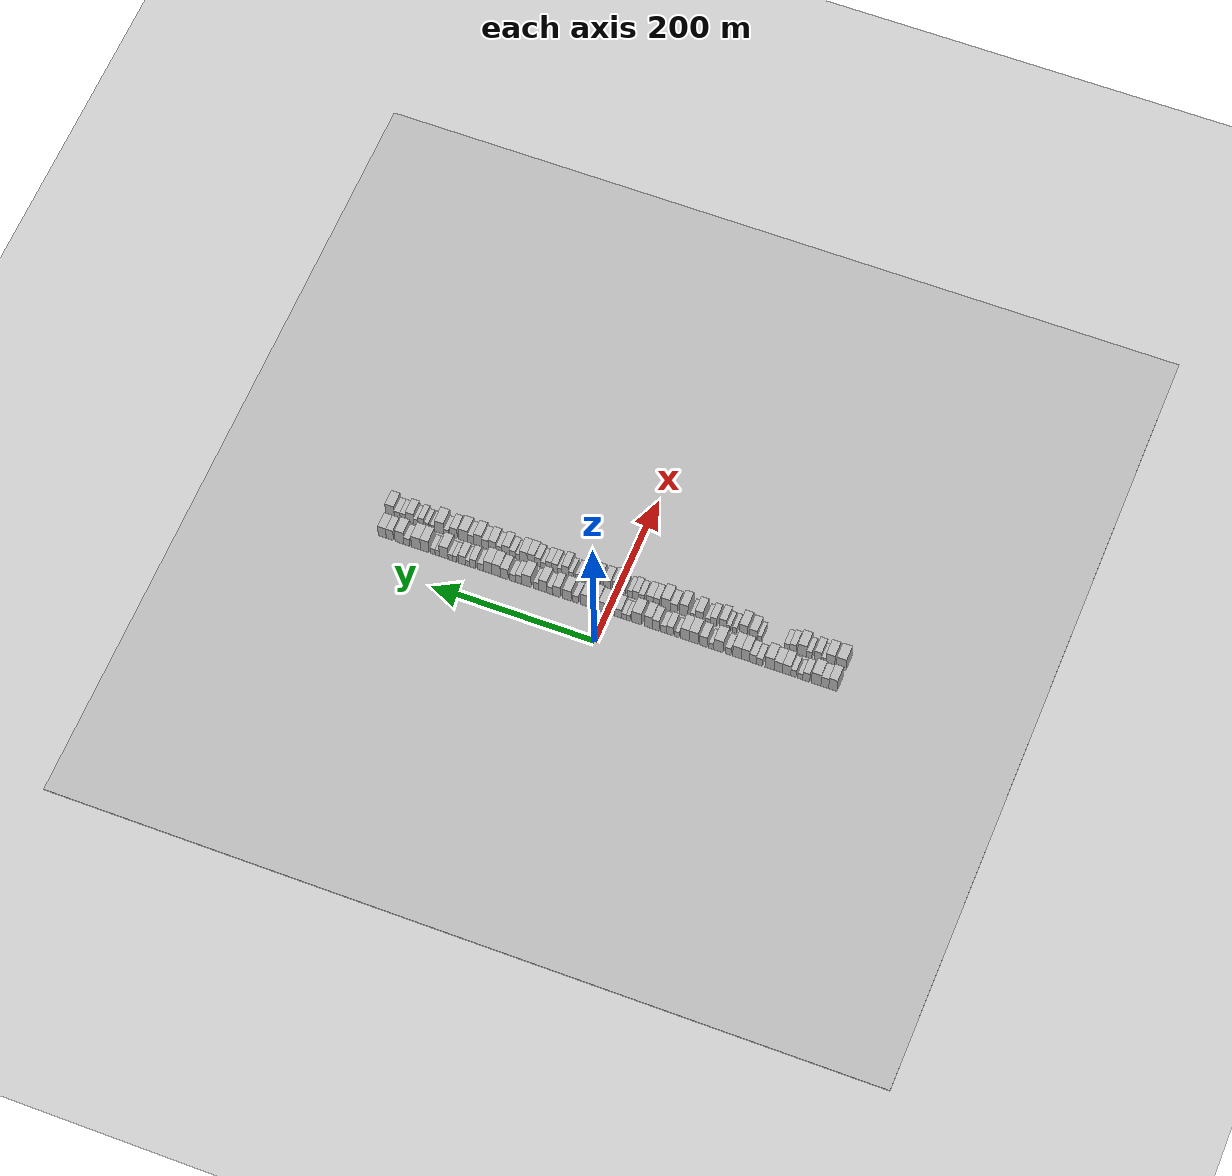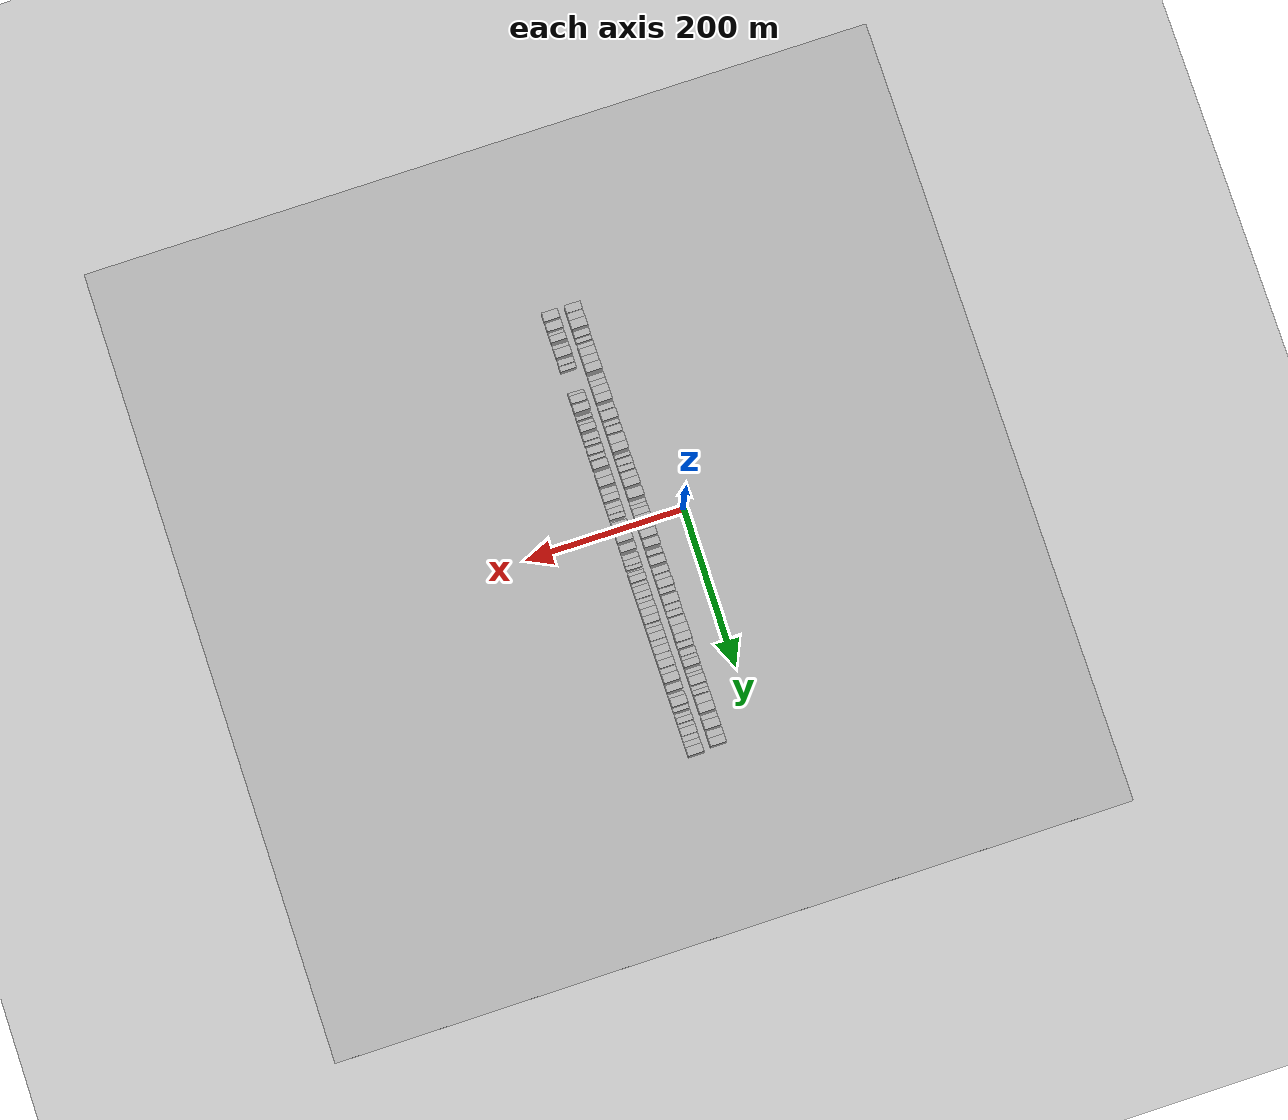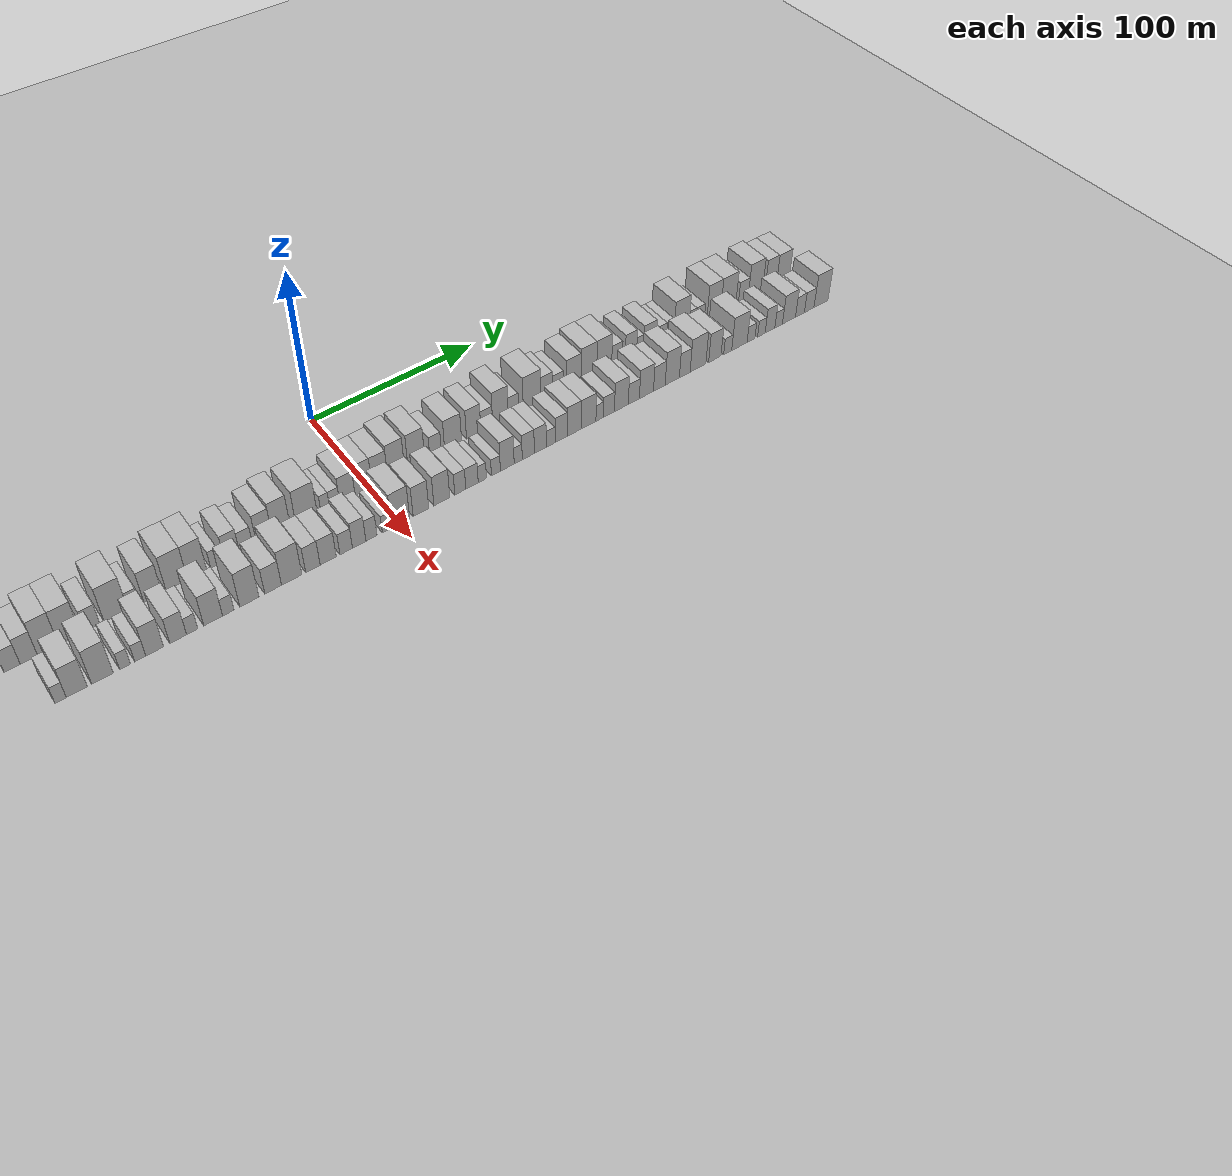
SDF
<?xml version="1.0" encoding="utf-8"?>

<sdf version="1.6">

   <world name="default">

      <gui fullscreen="0">

         <camera name="user_camera">

            <pose>-15 0 4.57585 0 0 0</pose>

            <view_controller>orbit</view_controller>

         </camera>

      </gui>

      <scene>

         <sky>

           <clouds>

             <speed>12</speed>

           </clouds>

         </sky>

         <ambient>0.4 0.4 0.4 1</ambient>

         <background>0.7 0.7 0.7 1</background>

         <shadows>1</shadows>

      </scene>

      <gravity>0 0 -9.8066</gravity>

      <magnetic_field>6e-06 2.3e-05 -4.2e-05</magnetic_field>

      <physics default="0" name="default_physics" type="ode">

         <ode>

            <solver>

               <type>quick</type>

               <iters>10</iters>

               <sor>1.0</sor>

               <use_dynamic_moi_rescaling>0</use_dynamic_moi_rescaling>

            </solver>

            <constraints>

               <cfm>0</cfm>

               <erp>0.2</erp>

               <contact_max_correcting_vel>100</contact_max_correcting_vel>

               <contact_surface_layer>0.001</contact_surface_layer>

            </constraints>

         </ode>

         <max_step_size>0.004</max_step_size>

         <real_time_factor>1</real_time_factor>

         <real_time_update_rate>250</real_time_update_rate>

      </physics>

      <light name="sun" type="directional">

         <cast_shadows>1</cast_shadows>

         <pose>0 0 10 0 0 0</pose>

         <diffuse>0.8 0.8 0.8 1</diffuse>

         <specular>0.2 0.2 0.2 1</specular>

         <attenuation>

            <range>1000</range>

            <constant>0.9</constant>

            <linear>0.01</linear>

            <quadratic>0.001</quadratic>

         </attenuation>

         <direction>-0.5 0.1 -0.9</direction>

      </light>

      <include>

         <name>ground_plane_1</name>

         <uri>model://HANNAS_ground_plane</uri>

         <pose>0 0 0  0 0 0</pose>

      </include>

      <include>

         <name>ground_plane_2</name>

         <uri>model://HANNAS_ground_plane</uri>

         <pose>100 0 0  0 0 0</pose>

      </include>

      <model name="building_1">

         <static>1</static>

         <pose frame="">50.0000 -272.9200 0 0.000000 0.000000 0.000000</pose>

         <link name="link">

            <pose frame="">0 0 12.00 0 0 0</pose>

            <collision name="collision">

               <geometry>

                  <box>

                     <size>20.0000 10.1599 24.0000</size>

                  </box>

               </geometry>

               <max_contacts>10</max_contacts>

               <surface>

                  <contact>

                     <ode/>

                  </contact>

                  <bounce/>

                  <friction>

                     <torsional>

                        <ode/>

                     </torsional>

                     <ode/>

                  </friction>

               </surface>

            </collision>

            <visual name="visual">

               <cast_shadows>0</cast_shadows>

               <geometry>

                  <box>

                     <size>20.0000 10.1599 24.0000</size>

                  </box>

               </geometry>

               <material>

                  <script>

                     <uri>model://HANNAS_wall/materials/scripts</uri>

                     <uri>model://HANNAS_wall/materials/textures</uri>

                     <name>vrc/HANNAS_wall</name>

                  </script>

               </material>

            </visual>

            <self_collide>0</self_collide>

            <enable_wind>0</enable_wind>

            <kinematic>0</kinematic>

         </link>

      </model>

      <model name="building_2">

         <static>1</static>

         <pose frame="">50.0000 -263.1600 0 0.000000 0.000000 0.000000</pose>

         <link name="link">

            <pose frame="">0 0 10.50 0 0 0</pose>

            <collision name="collision">

               <geometry>

                  <box>

                     <size>20.0000 9.3602 21.0000</size>

                  </box>

               </geometry>

               <max_contacts>10</max_contacts>

               <surface>

                  <contact>

                     <ode/>

                  </contact>

                  <bounce/>

                  <friction>

                     <torsional>

                        <ode/>

                     </torsional>

                     <ode/>

                  </friction>

               </surface>

            </collision>

            <visual name="visual">

               <cast_shadows>0</cast_shadows>

               <geometry>

                  <box>

                     <size>20.0000 9.3602 21.0000</size>

                  </box>

               </geometry>

               <material>

                  <script>

                     <uri>model://HANNAS_wall/materials/scripts</uri>

                     <uri>model://HANNAS_wall/materials/textures</uri>

                     <name>vrc/HANNAS_wall</name>

                  </script>

               </material>

            </visual>

            <self_collide>0</self_collide>

            <enable_wind>0</enable_wind>

            <kinematic>0</kinematic>

         </link>

      </model>

      <model name="building_3">

         <static>1</static>

         <pose frame="">50.0000 -252.7871 0 0.000000 0.000000 0.000000</pose>

         <link name="link">

            <pose frame="">0 0 12.00 0 0 0</pose>

            <collision name="collision">

               <geometry>

                  <box>

                     <size>20.0000 11.3856 24.0000</size>

                  </box>

               </geometry>

               <max_contacts>10</max_contacts>

               <surface>

                  <contact>

                     <ode/>

                  </contact>

                  <bounce/>

                  <friction>

                     <torsional>

                        <ode/>

                     </torsional>

                     <ode/>

                  </friction>

               </surface>

            </collision>

            <visual name="visual">

               <cast_shadows>0</cast_shadows>

               <geometry>

                  <box>

                     <size>20.0000 11.3856 24.0000</size>

                  </box>

               </geometry>

               <material>

                  <script>

                     <uri>model://HANNAS_wall/materials/scripts</uri>

                     <uri>model://HANNAS_wall/materials/textures</uri>

                     <name>vrc/HANNAS_wall</name>

                  </script>

               </material>

            </visual>

            <self_collide>0</self_collide>

            <enable_wind>0</enable_wind>

            <kinematic>0</kinematic>

         </link>

      </model>

      <model name="building_4">

         <static>1</static>

         <pose frame="">50.0000 -240.8640 0 0.000000 0.000000 0.000000</pose>

         <link name="link">

            <pose frame="">0 0 9.00 0 0 0</pose>

            <collision name="collision">

               <geometry>

                  <box>

                     <size>20.0000 8.4605 18.0000</size>

                  </box>

               </geometry>

               <max_contacts>10</max_contacts>

               <surface>

                  <contact>

                     <ode/>

                  </contact>

                  <bounce/>

                  <friction>

                     <torsional>

                        <ode/>

                     </torsional>

                     <ode/>

                  </friction>

               </surface>

            </collision>

            <visual name="visual">

               <cast_shadows>0</cast_shadows>

               <geometry>

                  <box>

                     <size>20.0000 8.4605 18.0000</size>

                  </box>

               </geometry>

               <material>

                  <script>

                     <uri>model://HANNAS_wall/materials/scripts</uri>

                     <uri>model://HANNAS_wall/materials/textures</uri>

                     <name>vrc/HANNAS_wall</name>

                  </script>

               </material>

            </visual>

            <self_collide>0</self_collide>

            <enable_wind>0</enable_wind>

            <kinematic>0</kinematic>

         </link>

      </model>

      <model name="building_5">

         <static>1</static>

         <pose frame="">50.0000 -233.6953 0 0.000000 0.000000 0.000000</pose>

         <link name="link">

            <pose frame="">0 0 6.00 0 0 0</pose>

            <collision name="collision">

               <geometry>

                  <box>

                     <size>20.0000 5.8770 12.0000</size>

                  </box>

               </geometry>

               <max_contacts>10</max_contacts>

               <surface>

                  <contact>

                     <ode/>

                  </contact>

                  <bounce/>

                  <friction>

                     <torsional>

                        <ode/>

                     </torsional>

                     <ode/>

                  </friction>

               </surface>

            </collision>

            <visual name="visual">

               <cast_shadows>0</cast_shadows>

               <geometry>

                  <box>

                     <size>20.0000 5.8770 12.0000</size>

                  </box>

               </geometry>

               <material>

                  <script>

                     <uri>model://HANNAS_wall/materials/scripts</uri>

                     <uri>model://HANNAS_wall/materials/textures</uri>

                     <name>vrc/HANNAS_wall</name>

                  </script>

               </material>

            </visual>

            <self_collide>0</self_collide>

            <enable_wind>0</enable_wind>

            <kinematic>0</kinematic>

         </link>

      </model>

      <model name="building_6">

         <static>1</static>

         <pose frame="">50.0000 -225.4794 0 0.000000 0.000000 0.000000</pose>

         <link name="link">

            <pose frame="">0 0 7.50 0 0 0</pose>

            <collision name="collision">

               <geometry>

                  <box>

                     <size>20.0000 6.5549 15.0000</size>

                  </box>

               </geometry>

               <max_contacts>10</max_contacts>

               <surface>

                  <contact>

                     <ode/>

                  </contact>

                  <bounce/>

                  <friction>

                     <torsional>

                        <ode/>

                     </torsional>

                     <ode/>

                  </friction>

               </surface>

            </collision>

            <visual name="visual">

               <cast_shadows>0</cast_shadows>

               <geometry>

                  <box>

                     <size>20.0000 6.5549 15.0000</size>

                  </box>

               </geometry>

               <material>

                  <script>

                     <uri>model://HANNAS_wall/materials/scripts</uri>

                     <uri>model://HANNAS_wall/materials/textures</uri>

                     <name>vrc/HANNAS_wall</name>

                  </script>

               </material>

            </visual>

            <self_collide>0</self_collide>

            <enable_wind>0</enable_wind>

            <kinematic>0</kinematic>

         </link>

      </model>

      <model name="building_7">

         <static>1</static>

         <pose frame="">50.0000 -217.2844 0 0.000000 0.000000 0.000000</pose>

         <link name="link">

            <pose frame="">0 0 10.50 0 0 0</pose>

            <collision name="collision">

               <geometry>

                  <box>

                     <size>20.0000 9.8351 21.0000</size>

                  </box>

               </geometry>

               <max_contacts>10</max_contacts>

               <surface>

                  <contact>

                     <ode/>

                  </contact>

                  <bounce/>

                  <friction>

                     <torsional>

                        <ode/>

                     </torsional>

                     <ode/>

                  </friction>

               </surface>

            </collision>

            <visual name="visual">

               <cast_shadows>0</cast_shadows>

               <geometry>

                  <box>

                     <size>20.0000 9.8351 21.0000</size>

                  </box>

               </geometry>

               <material>

                  <script>

                     <uri>model://HANNAS_wall/materials/scripts</uri>

                     <uri>model://HANNAS_wall/materials/textures</uri>

                     <name>vrc/HANNAS_wall</name>

                  </script>

               </material>

            </visual>

            <self_collide>0</self_collide>

            <enable_wind>0</enable_wind>

            <kinematic>0</kinematic>

         </link>

      </model>

      <model name="building_8">

         <static>1</static>

         <pose frame="">50.0000 -207.2221 0 0.000000 0.000000 0.000000</pose>

         <link name="link">

            <pose frame="">0 0 10.50 0 0 0</pose>

            <collision name="collision">

               <geometry>

                  <box>

                     <size>20.0000 10.2895 21.0000</size>

                  </box>

               </geometry>

               <max_contacts>10</max_contacts>

               <surface>

                  <contact>

                     <ode/>

                  </contact>

                  <bounce/>

                  <friction>

                     <torsional>

                        <ode/>

                     </torsional>

                     <ode/>

                  </friction>

               </surface>

            </collision>

            <visual name="visual">

               <cast_shadows>0</cast_shadows>

               <geometry>

                  <box>

                     <size>20.0000 10.2895 21.0000</size>

                  </box>

               </geometry>

               <material>

                  <script>

                     <uri>model://HANNAS_wall/materials/scripts</uri>

                     <uri>model://HANNAS_wall/materials/textures</uri>

                     <name>vrc/HANNAS_wall</name>

                  </script>

               </material>

            </visual>

            <self_collide>0</self_collide>

            <enable_wind>0</enable_wind>

            <kinematic>0</kinematic>

         </link>

      </model>

      <model name="building_9">

         <static>1</static>

         <pose frame="">50.0000 -196.6177 0 0.000000 0.000000 0.000000</pose>

         <link name="link">

            <pose frame="">0 0 12.00 0 0 0</pose>

            <collision name="collision">

               <geometry>

                  <box>

                     <size>20.0000 10.9194 24.0000</size>

                  </box>

               </geometry>

               <max_contacts>10</max_contacts>

               <surface>

                  <contact>

                     <ode/>

                  </contact>

                  <bounce/>

                  <friction>

                     <torsional>

                        <ode/>

                     </torsional>

                     <ode/>

                  </friction>

               </surface>

            </collision>

            <visual name="visual">

               <cast_shadows>0</cast_shadows>

               <geometry>

                  <box>

                     <size>20.0000 10.9194 24.0000</size>

                  </box>

               </geometry>

               <material>

                  <script>

                     <uri>model://HANNAS_wall/materials/scripts</uri>

                     <uri>model://HANNAS_wall/materials/textures</uri>

                     <name>vrc/HANNAS_wall</name>

                  </script>

               </material>

            </visual>

            <self_collide>0</self_collide>

            <enable_wind>0</enable_wind>

            <kinematic>0</kinematic>

         </link>

      </model>

      <model name="building_10">

         <static>1</static>

         <pose frame="">50.0000 -184.4147 0 0.000000 0.000000 0.000000</pose>

         <link name="link">

            <pose frame="">0 0 7.50 0 0 0</pose>

            <collision name="collision">

               <geometry>

                  <box>

                     <size>20.0000 7.4866 15.0000</size>

                  </box>

               </geometry>

               <max_contacts>10</max_contacts>

               <surface>

                  <contact>

                     <ode/>

                  </contact>

                  <bounce/>

                  <friction>

                     <torsional>

                        <ode/>

                     </torsional>

                     <ode/>

                  </friction>

               </surface>

            </collision>

            <visual name="visual">

               <cast_shadows>0</cast_shadows>

               <geometry>

                  <box>

                     <size>20.0000 7.4866 15.0000</size>

                  </box>

               </geometry>

               <material>

                  <script>

                     <uri>model://HANNAS_wall/materials/scripts</uri>

                     <uri>model://HANNAS_wall/materials/textures</uri>

                     <name>vrc/HANNAS_wall</name>

                  </script>

               </material>

            </visual>

            <self_collide>0</self_collide>

            <enable_wind>0</enable_wind>

            <kinematic>0</kinematic>

         </link>

      </model>

      <model name="building_11">

         <static>1</static>

         <pose frame="">50.0000 -176.6504 0 0.000000 0.000000 0.000000</pose>

         <link name="link">

            <pose frame="">0 0 9.00 0 0 0</pose>

            <collision name="collision">

               <geometry>

                  <box>

                     <size>20.0000 8.0421 18.0000</size>

                  </box>

               </geometry>

               <max_contacts>10</max_contacts>

               <surface>

                  <contact>

                     <ode/>

                  </contact>

                  <bounce/>

                  <friction>

                     <torsional>

                        <ode/>

                     </torsional>

                     <ode/>

                  </friction>

               </surface>

            </collision>

            <visual name="visual">

               <cast_shadows>0</cast_shadows>

               <geometry>

                  <box>

                     <size>20.0000 8.0421 18.0000</size>

                  </box>

               </geometry>

               <material>

                  <script>

                     <uri>model://HANNAS_wall/materials/scripts</uri>

                     <uri>model://HANNAS_wall/materials/textures</uri>

                     <name>vrc/HANNAS_wall</name>

                  </script>

               </material>

            </visual>

            <self_collide>0</self_collide>

            <enable_wind>0</enable_wind>

            <kinematic>0</kinematic>

         </link>

      </model>

      <model name="building_12">

         <static>1</static>

         <pose frame="">50.0000 -167.6863 0 0.000000 0.000000 0.000000</pose>

         <link name="link">

            <pose frame="">0 0 12.00 0 0 0</pose>

            <collision name="collision">

               <geometry>

                  <box>

                     <size>20.0000 9.8860 24.0000</size>

                  </box>

               </geometry>

               <max_contacts>10</max_contacts>

               <surface>

                  <contact>

                     <ode/>

                  </contact>

                  <bounce/>

                  <friction>

                     <torsional>

                        <ode/>

                     </torsional>

                     <ode/>

                  </friction>

               </surface>

            </collision>

            <visual name="visual">

               <cast_shadows>0</cast_shadows>

               <geometry>

                  <box>

                     <size>20.0000 9.8860 24.0000</size>

                  </box>

               </geometry>

               <material>

                  <script>

                     <uri>model://HANNAS_wall/materials/scripts</uri>

                     <uri>model://HANNAS_wall/materials/textures</uri>

                     <name>vrc/HANNAS_wall</name>

                  </script>

               </material>

            </visual>

            <self_collide>0</self_collide>

            <enable_wind>0</enable_wind>

            <kinematic>0</kinematic>

         </link>

      </model>

      <model name="building_13">

         <static>1</static>

         <pose frame="">50.0000 -157.5218 0 0.000000 0.000000 0.000000</pose>

         <link name="link">

            <pose frame="">0 0 12.00 0 0 0</pose>

            <collision name="collision">

               <geometry>

                  <box>

                     <size>20.0000 10.4430 24.0000</size>

                  </box>

               </geometry>

               <max_contacts>10</max_contacts>

               <surface>

                  <contact>

                     <ode/>

                  </contact>

                  <bounce/>

                  <friction>

                     <torsional>

                        <ode/>

                     </torsional>

                     <ode/>

                  </friction>

               </surface>

            </collision>

            <visual name="visual">

               <cast_shadows>0</cast_shadows>

               <geometry>

                  <box>

                     <size>20.0000 10.4430 24.0000</size>

                  </box>

               </geometry>

               <material>

                  <script>

                     <uri>model://HANNAS_wall/materials/scripts</uri>

                     <uri>model://HANNAS_wall/materials/textures</uri>

                     <name>vrc/HANNAS_wall</name>

                  </script>

               </material>

            </visual>

            <self_collide>0</self_collide>

            <enable_wind>0</enable_wind>

            <kinematic>0</kinematic>

         </link>

      </model>

      <model name="building_14">

         <static>1</static>

         <pose frame="">50.0000 -146.6202 0 0.000000 0.000000 0.000000</pose>

         <link name="link">

            <pose frame="">0 0 7.50 0 0 0</pose>

            <collision name="collision">

               <geometry>

                  <box>

                     <size>20.0000 7.3601 15.0000</size>

                  </box>

               </geometry>

               <max_contacts>10</max_contacts>

               <surface>

                  <contact>

                     <ode/>

                  </contact>

                  <bounce/>

                  <friction>

                     <torsional>

                        <ode/>

                     </torsional>

                     <ode/>

                  </friction>

               </surface>

            </collision>

            <visual name="visual">

               <cast_shadows>0</cast_shadows>

               <geometry>

                  <box>

                     <size>20.0000 7.3601 15.0000</size>

                  </box>

               </geometry>

               <material>

                  <script>

                     <uri>model://HANNAS_wall/materials/scripts</uri>

                     <uri>model://HANNAS_wall/materials/textures</uri>

                     <name>vrc/HANNAS_wall</name>

                  </script>

               </material>

            </visual>

            <self_collide>0</self_collide>

            <enable_wind>0</enable_wind>

            <kinematic>0</kinematic>

         </link>

      </model>

      <model name="building_15">

         <static>1</static>

         <pose frame="">50.0000 -135.1217 0 0.000000 0.000000 0.000000</pose>

         <link name="link">

            <pose frame="">0 0 12.00 0 0 0</pose>

            <collision name="collision">

               <geometry>

                  <box>

                     <size>20.0000 11.6370 24.0000</size>

                  </box>

               </geometry>

               <max_contacts>10</max_contacts>

               <surface>

                  <contact>

                     <ode/>

                  </contact>

                  <bounce/>

                  <friction>

                     <torsional>

                        <ode/>

                     </torsional>

                     <ode/>

                  </friction>

               </surface>

            </collision>

            <visual name="visual">

               <cast_shadows>0</cast_shadows>

               <geometry>

                  <box>

                     <size>20.0000 11.6370 24.0000</size>

                  </box>

               </geometry>

               <material>

                  <script>

                     <uri>model://HANNAS_wall/materials/scripts</uri>

                     <uri>model://HANNAS_wall/materials/textures</uri>

                     <name>vrc/HANNAS_wall</name>

                  </script>

               </material>

            </visual>

            <self_collide>0</self_collide>

            <enable_wind>0</enable_wind>

            <kinematic>0</kinematic>

         </link>

      </model>

      <model name="building_16">

         <static>1</static>

         <pose frame="">50.0000 -126.3583 0 0.000000 0.000000 0.000000</pose>

         <link name="link">

            <pose frame="">0 0 6.00 0 0 0</pose>

            <collision name="collision">

               <geometry>

                  <box>

                     <size>20.0000 5.8898 12.0000</size>

                  </box>

               </geometry>

               <max_contacts>10</max_contacts>

               <surface>

                  <contact>

                     <ode/>

                  </contact>

                  <bounce/>

                  <friction>

                     <torsional>

                        <ode/>

                     </torsional>

                     <ode/>

                  </friction>

               </surface>

            </collision>

            <visual name="visual">

               <cast_shadows>0</cast_shadows>

               <geometry>

                  <box>

                     <size>20.0000 5.8898 12.0000</size>

                  </box>

               </geometry>

               <material>

                  <script>

                     <uri>model://HANNAS_wall/materials/scripts</uri>

                     <uri>model://HANNAS_wall/materials/textures</uri>

                     <name>vrc/HANNAS_wall</name>

                  </script>

               </material>

            </visual>

            <self_collide>0</self_collide>

            <enable_wind>0</enable_wind>

            <kinematic>0</kinematic>

         </link>

      </model>

      <model name="building_17">

         <static>1</static>

         <pose frame="">50.0000 -116.8223 0 0.000000 0.000000 0.000000</pose>

         <link name="link">

            <pose frame="">0 0 10.50 0 0 0</pose>

            <collision name="collision">

               <geometry>

                  <box>

                     <size>20.0000 9.1821 21.0000</size>

                  </box>

               </geometry>

               <max_contacts>10</max_contacts>

               <surface>

                  <contact>

                     <ode/>

                  </contact>

                  <bounce/>

                  <friction>

                     <torsional>

                        <ode/>

                     </torsional>

                     <ode/>

                  </friction>

               </surface>

            </collision>

            <visual name="visual">

               <cast_shadows>0</cast_shadows>

               <geometry>

                  <box>

                     <size>20.0000 9.1821 21.0000</size>

                  </box>

               </geometry>

               <material>

                  <script>

                     <uri>model://HANNAS_wall/materials/scripts</uri>

                     <uri>model://HANNAS_wall/materials/textures</uri>

                     <name>vrc/HANNAS_wall</name>

                  </script>

               </material>

            </visual>

            <self_collide>0</self_collide>

            <enable_wind>0</enable_wind>

            <kinematic>0</kinematic>

         </link>

      </model>

      <model name="building_18">

         <static>1</static>

         <pose frame="">50.0000 -104.7328 0 0.000000 0.000000 0.000000</pose>

         <link name="link">

            <pose frame="">0 0 12.00 0 0 0</pose>

            <collision name="collision">

               <geometry>

                  <box>

                     <size>20.0000 10.9970 24.0000</size>

                  </box>

               </geometry>

               <max_contacts>10</max_contacts>

               <surface>

                  <contact>

                     <ode/>

                  </contact>

                  <bounce/>

                  <friction>

                     <torsional>

                        <ode/>

                     </torsional>

                     <ode/>

                  </friction>

               </surface>

            </collision>

            <visual name="visual">

               <cast_shadows>0</cast_shadows>

               <geometry>

                  <box>

                     <size>20.0000 10.9970 24.0000</size>

                  </box>

               </geometry>

               <material>

                  <script>

                     <uri>model://HANNAS_wall/materials/scripts</uri>

                     <uri>model://HANNAS_wall/materials/textures</uri>

                     <name>vrc/HANNAS_wall</name>

                  </script>

               </material>

            </visual>

            <self_collide>0</self_collide>

            <enable_wind>0</enable_wind>

            <kinematic>0</kinematic>

         </link>

      </model>

      <model name="building_19">

         <static>1</static>

         <pose frame="">50.0000 -94.2725 0 0.000000 0.000000 0.000000</pose>

         <link name="link">

            <pose frame="">0 0 12.00 0 0 0</pose>

            <collision name="collision">

               <geometry>

                  <box>

                     <size>20.0000 9.9236 24.0000</size>

                  </box>

               </geometry>

               <max_contacts>10</max_contacts>

               <surface>

                  <contact>

                     <ode/>

                  </contact>

                  <bounce/>

                  <friction>

                     <torsional>

                        <ode/>

                     </torsional>

                     <ode/>

                  </friction>

               </surface>

            </collision>

            <visual name="visual">

               <cast_shadows>0</cast_shadows>

               <geometry>

                  <box>

                     <size>20.0000 9.9236 24.0000</size>

                  </box>

               </geometry>

               <material>

                  <script>

                     <uri>model://HANNAS_wall/materials/scripts</uri>

                     <uri>model://HANNAS_wall/materials/textures</uri>

                     <name>vrc/HANNAS_wall</name>

                  </script>

               </material>

            </visual>

            <self_collide>0</self_collide>

            <enable_wind>0</enable_wind>

            <kinematic>0</kinematic>

         </link>

      </model>

      <model name="building_20">

         <static>1</static>

         <pose frame="">50.0000 -84.7162 0 0.000000 0.000000 0.000000</pose>

         <link name="link">

            <pose frame="">0 0 6.00 0 0 0</pose>

            <collision name="collision">

               <geometry>

                  <box>

                     <size>20.0000 5.1888 12.0000</size>

                  </box>

               </geometry>

               <max_contacts>10</max_contacts>

               <surface>

                  <contact>

                     <ode/>

                  </contact>

                  <bounce/>

                  <friction>

                     <torsional>

                        <ode/>

                     </torsional>

                     <ode/>

                  </friction>

               </surface>

            </collision>

            <visual name="visual">

               <cast_shadows>0</cast_shadows>

               <geometry>

                  <box>

                     <size>20.0000 5.1888 12.0000</size>

                  </box>

               </geometry>

               <material>

                  <script>

                     <uri>model://HANNAS_wall/materials/scripts</uri>

                     <uri>model://HANNAS_wall/materials/textures</uri>

                     <name>vrc/HANNAS_wall</name>

                  </script>

               </material>

            </visual>

            <self_collide>0</self_collide>

            <enable_wind>0</enable_wind>

            <kinematic>0</kinematic>

         </link>

      </model>

      <model name="building_21">

         <static>1</static>

         <pose frame="">50.0000 -76.0519 0 0.000000 0.000000 0.000000</pose>

         <link name="link">

            <pose frame="">0 0 9.00 0 0 0</pose>

            <collision name="collision">

               <geometry>

                  <box>

                     <size>20.0000 8.1398 18.0000</size>

                  </box>

               </geometry>

               <max_contacts>10</max_contacts>

               <surface>

                  <contact>

                     <ode/>

                  </contact>

                  <bounce/>

                  <friction>

                     <torsional>

                        <ode/>

                     </torsional>

                     <ode/>

                  </friction>

               </surface>

            </collision>

            <visual name="visual">

               <cast_shadows>0</cast_shadows>

               <geometry>

                  <box>

                     <size>20.0000 8.1398 18.0000</size>

                  </box>

               </geometry>

               <material>

                  <script>

                     <uri>model://HANNAS_wall/materials/scripts</uri>

                     <uri>model://HANNAS_wall/materials/textures</uri>

                     <name>vrc/HANNAS_wall</name>

                  </script>

               </material>

            </visual>

            <self_collide>0</self_collide>

            <enable_wind>0</enable_wind>

            <kinematic>0</kinematic>

         </link>

      </model>

      <model name="building_22">

         <static>1</static>

         <pose frame="">50.0000 -68.4234 0 0.000000 0.000000 0.000000</pose>

         <link name="link">

            <pose frame="">0 0 7.50 0 0 0</pose>

            <collision name="collision">

               <geometry>

                  <box>

                     <size>20.0000 7.1172 15.0000</size>

                  </box>

               </geometry>

               <max_contacts>10</max_contacts>

               <surface>

                  <contact>

                     <ode/>

                  </contact>

                  <bounce/>

                  <friction>

                     <torsional>

                        <ode/>

                     </torsional>

                     <ode/>

                  </friction>

               </surface>

            </collision>

            <visual name="visual">

               <cast_shadows>0</cast_shadows>

               <geometry>

                  <box>

                     <size>20.0000 7.1172 15.0000</size>

                  </box>

               </geometry>

               <material>

                  <script>

                     <uri>model://HANNAS_wall/materials/scripts</uri>

                     <uri>model://HANNAS_wall/materials/textures</uri>

                     <name>vrc/HANNAS_wall</name>

                  </script>

               </material>

            </visual>

            <self_collide>0</self_collide>

            <enable_wind>0</enable_wind>

            <kinematic>0</kinematic>

         </link>

      </model>

      <model name="building_23">

         <static>1</static>

         <pose frame="">50.0000 -58.6308 0 0.000000 0.000000 0.000000</pose>

         <link name="link">

            <pose frame="">0 0 10.50 0 0 0</pose>

            <collision name="collision">

               <geometry>

                  <box>

                     <size>20.0000 8.4679 21.0000</size>

                  </box>

               </geometry>

               <max_contacts>10</max_contacts>

               <surface>

                  <contact>

                     <ode/>

                  </contact>

                  <bounce/>

                  <friction>

                     <torsional>

                        <ode/>

                     </torsional>

                     <ode/>

                  </friction>

               </surface>

            </collision>

            <visual name="visual">

               <cast_shadows>0</cast_shadows>

               <geometry>

                  <box>

                     <size>20.0000 8.4679 21.0000</size>

                  </box>

               </geometry>

               <material>

                  <script>

                     <uri>model://HANNAS_wall/materials/scripts</uri>

                     <uri>model://HANNAS_wall/materials/textures</uri>

                     <name>vrc/HANNAS_wall</name>

                  </script>

               </material>

            </visual>

            <self_collide>0</self_collide>

            <enable_wind>0</enable_wind>

            <kinematic>0</kinematic>

         </link>

      </model>

      <model name="building_24">

         <static>1</static>

         <pose frame="">50.0000 -49.4877 0 0.000000 0.000000 0.000000</pose>

         <link name="link">

            <pose frame="">0 0 12.00 0 0 0</pose>

            <collision name="collision">

               <geometry>

                  <box>

                     <size>20.0000 9.8183 24.0000</size>

                  </box>

               </geometry>

               <max_contacts>10</max_contacts>

               <surface>

                  <contact>

                     <ode/>

                  </contact>

                  <bounce/>

                  <friction>

                     <torsional>

                        <ode/>

                     </torsional>

                     <ode/>

                  </friction>

               </surface>

            </collision>

            <visual name="visual">

               <cast_shadows>0</cast_shadows>

               <geometry>

                  <box>

                     <size>20.0000 9.8183 24.0000</size>

                  </box>

               </geometry>

               <material>

                  <script>

                     <uri>model://HANNAS_wall/materials/scripts</uri>

                     <uri>model://HANNAS_wall/materials/textures</uri>

                     <name>vrc/HANNAS_wall</name>

                  </script>

               </material>

            </visual>

            <self_collide>0</self_collide>

            <enable_wind>0</enable_wind>

            <kinematic>0</kinematic>

         </link>

      </model>

      <model name="building_25">

         <static>1</static>

         <pose frame="">50.0000 -35.6482 0 0.000000 0.000000 0.000000</pose>

         <link name="link">

            <pose frame="">0 0 12.00 0 0 0</pose>

            <collision name="collision">

               <geometry>

                  <box>

                     <size>20.0000 11.8606 24.0000</size>

                  </box>

               </geometry>

               <max_contacts>10</max_contacts>

               <surface>

                  <contact>

                     <ode/>

                  </contact>

                  <bounce/>

                  <friction>

                     <torsional>

                        <ode/>

                     </torsional>

                     <ode/>

                  </friction>

               </surface>

            </collision>

            <visual name="visual">

               <cast_shadows>0</cast_shadows>

               <geometry>

                  <box>

                     <size>20.0000 11.8606 24.0000</size>

                  </box>

               </geometry>

               <material>

                  <script>

                     <uri>model://HANNAS_wall/materials/scripts</uri>

                     <uri>model://HANNAS_wall/materials/textures</uri>

                     <name>vrc/HANNAS_wall</name>

                  </script>

               </material>

            </visual>

            <self_collide>0</self_collide>

            <enable_wind>0</enable_wind>

            <kinematic>0</kinematic>

         </link>

      </model>

      <model name="building_26">

         <static>1</static>

         <pose frame="">50.0000 -25.2976 0 0.000000 0.000000 0.000000</pose>

         <link name="link">

            <pose frame="">0 0 6.00 0 0 0</pose>

            <collision name="collision">

               <geometry>

                  <box>

                     <size>20.0000 4.8406 12.0000</size>

                  </box>

               </geometry>

               <max_contacts>10</max_contacts>

               <surface>

                  <contact>

                     <ode/>

                  </contact>

                  <bounce/>

                  <friction>

                     <torsional>

                        <ode/>

                     </torsional>

                     <ode/>

                  </friction>

               </surface>

            </collision>

            <visual name="visual">

               <cast_shadows>0</cast_shadows>

               <geometry>

                  <box>

                     <size>20.0000 4.8406 12.0000</size>

                  </box>

               </geometry>

               <material>

                  <script>

                     <uri>model://HANNAS_wall/materials/scripts</uri>

                     <uri>model://HANNAS_wall/materials/textures</uri>

                     <name>vrc/HANNAS_wall</name>

                  </script>

               </material>

            </visual>

            <self_collide>0</self_collide>

            <enable_wind>0</enable_wind>

            <kinematic>0</kinematic>

         </link>

      </model>

      <model name="building_27">

         <static>1</static>

         <pose frame="">50.0000 -20.0082 0 0.000000 0.000000 0.000000</pose>

         <link name="link">

            <pose frame="">0 0 6.00 0 0 0</pose>

            <collision name="collision">

               <geometry>

                  <box>

                     <size>20.0000 5.7383 12.0000</size>

                  </box>

               </geometry>

               <max_contacts>10</max_contacts>

               <surface>

                  <contact>

                     <ode/>

                  </contact>

                  <bounce/>

                  <friction>

                     <torsional>

                        <ode/>

                     </torsional>

                     <ode/>

                  </friction>

               </surface>

            </collision>

            <visual name="visual">

               <cast_shadows>0</cast_shadows>

               <geometry>

                  <box>

                     <size>20.0000 5.7383 12.0000</size>

                  </box>

               </geometry>

               <material>

                  <script>

                     <uri>model://HANNAS_wall/materials/scripts</uri>

                     <uri>model://HANNAS_wall/materials/textures</uri>

                     <name>vrc/HANNAS_wall</name>

                  </script>

               </material>

            </visual>

            <self_collide>0</self_collide>

            <enable_wind>0</enable_wind>

            <kinematic>0</kinematic>

         </link>

      </model>

      <model name="building_28">

         <static>1</static>

         <pose frame="">50.0000 -12.7895 0 0.000000 0.000000 0.000000</pose>

         <link name="link">

            <pose frame="">0 0 9.00 0 0 0</pose>

            <collision name="collision">

               <geometry>

                  <box>

                     <size>20.0000 8.6990 18.0000</size>

                  </box>

               </geometry>

               <max_contacts>10</max_contacts>

               <surface>

                  <contact>

                     <ode/>

                  </contact>

                  <bounce/>

                  <friction>

                     <torsional>

                        <ode/>

                     </torsional>

                     <ode/>

                  </friction>

               </surface>

            </collision>

            <visual name="visual">

               <cast_shadows>0</cast_shadows>

               <geometry>

                  <box>

                     <size>20.0000 8.6990 18.0000</size>

                  </box>

               </geometry>

               <material>

                  <script>

                     <uri>model://HANNAS_wall/materials/scripts</uri>

                     <uri>model://HANNAS_wall/materials/textures</uri>

                     <name>vrc/HANNAS_wall</name>

                  </script>

               </material>

            </visual>

            <self_collide>0</self_collide>

            <enable_wind>0</enable_wind>

            <kinematic>0</kinematic>

         </link>

      </model>

      <model name="building_29">

         <static>1</static>

         <pose frame="">50.0000 -3.5440 0 0.000000 0.000000 0.000000</pose>

         <link name="link">

            <pose frame="">0 0 10.50 0 0 0</pose>

            <collision name="collision">

               <geometry>

                  <box>

                     <size>20.0000 9.7920 21.0000</size>

                  </box>

               </geometry>

               <max_contacts>10</max_contacts>

               <surface>

                  <contact>

                     <ode/>

                  </contact>

                  <bounce/>

                  <friction>

                     <torsional>

                        <ode/>

                     </torsional>

                     <ode/>

                  </friction>

               </surface>

            </collision>

            <visual name="visual">

               <cast_shadows>0</cast_shadows>

               <geometry>

                  <box>

                     <size>20.0000 9.7920 21.0000</size>

                  </box>

               </geometry>

               <material>

                  <script>

                     <uri>model://HANNAS_wall/materials/scripts</uri>

                     <uri>model://HANNAS_wall/materials/textures</uri>

                     <name>vrc/HANNAS_wall</name>

                  </script>

               </material>

            </visual>

            <self_collide>0</self_collide>

            <enable_wind>0</enable_wind>

            <kinematic>0</kinematic>

         </link>

      </model>

      <model name="building_30">

         <static>1</static>

         <pose frame="">50.0000 5.9721 0 0.000000 0.000000 0.000000</pose>

         <link name="link">

            <pose frame="">0 0 10.50 0 0 0</pose>

            <collision name="collision">

               <geometry>

                  <box>

                     <size>20.0000 9.2402 21.0000</size>

                  </box>

               </geometry>

               <max_contacts>10</max_contacts>

               <surface>

                  <contact>

                     <ode/>

                  </contact>

                  <bounce/>

                  <friction>

                     <torsional>

                        <ode/>

                     </torsional>

                     <ode/>

                  </friction>

               </surface>

            </collision>

            <visual name="visual">

               <cast_shadows>0</cast_shadows>

               <geometry>

                  <box>

                     <size>20.0000 9.2402 21.0000</size>

                  </box>

               </geometry>

               <material>

                  <script>

                     <uri>model://HANNAS_wall/materials/scripts</uri>

                     <uri>model://HANNAS_wall/materials/textures</uri>

                     <name>vrc/HANNAS_wall</name>

                  </script>

               </material>

            </visual>

            <self_collide>0</self_collide>

            <enable_wind>0</enable_wind>

            <kinematic>0</kinematic>

         </link>

      </model>

      <model name="building_31">

         <static>1</static>

         <pose frame="">50.0000 15.5483 0 0.000000 0.000000 0.000000</pose>

         <link name="link">

            <pose frame="">0 0 12.00 0 0 0</pose>

            <collision name="collision">

               <geometry>

                  <box>

                     <size>20.0000 9.9122 24.0000</size>

                  </box>

               </geometry>

               <max_contacts>10</max_contacts>

               <surface>

                  <contact>

                     <ode/>

                  </contact>

                  <bounce/>

                  <friction>

                     <torsional>

                        <ode/>

                     </torsional>

                     <ode/>

                  </friction>

               </surface>

            </collision>

            <visual name="visual">

               <cast_shadows>0</cast_shadows>

               <geometry>

                  <box>

                     <size>20.0000 9.9122 24.0000</size>

                  </box>

               </geometry>

               <material>

                  <script>

                     <uri>model://HANNAS_wall/materials/scripts</uri>

                     <uri>model://HANNAS_wall/materials/textures</uri>

                     <name>vrc/HANNAS_wall</name>

                  </script>

               </material>

            </visual>

            <self_collide>0</self_collide>

            <enable_wind>0</enable_wind>

            <kinematic>0</kinematic>

         </link>

      </model>

      <model name="building_32">

         <static>1</static>

         <pose frame="">50.0000 27.4965 0 0.000000 0.000000 0.000000</pose>

         <link name="link">

            <pose frame="">0 0 12.00 0 0 0</pose>

            <collision name="collision">

               <geometry>

                  <box>

                     <size>20.0000 9.9842 24.0000</size>

                  </box>

               </geometry>

               <max_contacts>10</max_contacts>

               <surface>

                  <contact>

                     <ode/>

                  </contact>

                  <bounce/>

                  <friction>

                     <torsional>

                        <ode/>

                     </torsional>

                     <ode/>

                  </friction>

               </surface>

            </collision>

            <visual name="visual">

               <cast_shadows>0</cast_shadows>

               <geometry>

                  <box>

                     <size>20.0000 9.9842 24.0000</size>

                  </box>

               </geometry>

               <material>

                  <script>

                     <uri>model://HANNAS_wall/materials/scripts</uri>

                     <uri>model://HANNAS_wall/materials/textures</uri>

                     <name>vrc/HANNAS_wall</name>

                  </script>

               </material>

            </visual>

            <self_collide>0</self_collide>

            <enable_wind>0</enable_wind>

            <kinematic>0</kinematic>

         </link>

      </model>

      <model name="building_33">

         <static>1</static>

         <pose frame="">50.0000 38.9702 0 0.000000 0.000000 0.000000</pose>

         <link name="link">

            <pose frame="">0 0 7.50 0 0 0</pose>

            <collision name="collision">

               <geometry>

                  <box>

                     <size>20.0000 6.9632 15.0000</size>

                  </box>

               </geometry>

               <max_contacts>10</max_contacts>

               <surface>

                  <contact>

                     <ode/>

                  </contact>

                  <bounce/>

                  <friction>

                     <torsional>

                        <ode/>

                     </torsional>

                     <ode/>

                  </friction>

               </surface>

            </collision>

            <visual name="visual">

               <cast_shadows>0</cast_shadows>

               <geometry>

                  <box>

                     <size>20.0000 6.9632 15.0000</size>

                  </box>

               </geometry>

               <material>

                  <script>

                     <uri>model://HANNAS_wall/materials/scripts</uri>

                     <uri>model://HANNAS_wall/materials/textures</uri>

                     <name>vrc/HANNAS_wall</name>

                  </script>

               </material>

            </visual>

            <self_collide>0</self_collide>

            <enable_wind>0</enable_wind>

            <kinematic>0</kinematic>

         </link>

      </model>

      <model name="building_34">

         <static>1</static>

         <pose frame="">50.0000 49.6491 0 0.000000 0.000000 0.000000</pose>

         <link name="link">

            <pose frame="">0 0 10.50 0 0 0</pose>

            <collision name="collision">

               <geometry>

                  <box>

                     <size>20.0000 10.3947 21.0000</size>

                  </box>

               </geometry>

               <max_contacts>10</max_contacts>

               <surface>

                  <contact>

                     <ode/>

                  </contact>

                  <bounce/>

                  <friction>

                     <torsional>

                        <ode/>

                     </torsional>

                     <ode/>

                  </friction>

               </surface>

            </collision>

            <visual name="visual">

               <cast_shadows>0</cast_shadows>

               <geometry>

                  <box>

                     <size>20.0000 10.3947 21.0000</size>

                  </box>

               </geometry>

               <material>

                  <script>

                     <uri>model://HANNAS_wall/materials/scripts</uri>

                     <uri>model://HANNAS_wall/materials/textures</uri>

                     <name>vrc/HANNAS_wall</name>

                  </script>

               </material>

            </visual>

            <self_collide>0</self_collide>

            <enable_wind>0</enable_wind>

            <kinematic>0</kinematic>

         </link>

      </model>

      <model name="building_35">

         <static>1</static>

         <pose frame="">50.0000 62.3072 0 0.000000 0.000000 0.000000</pose>

         <link name="link">

            <pose frame="">0 0 10.50 0 0 0</pose>

            <collision name="collision">

               <geometry>

                  <box>

                     <size>20.0000 8.9213 21.0000</size>

                  </box>

               </geometry>

               <max_contacts>10</max_contacts>

               <surface>

                  <contact>

                     <ode/>

                  </contact>

                  <bounce/>

                  <friction>

                     <torsional>

                        <ode/>

                     </torsional>

                     <ode/>

                  </friction>

               </surface>

            </collision>

            <visual name="visual">

               <cast_shadows>0</cast_shadows>

               <geometry>

                  <box>

                     <size>20.0000 8.9213 21.0000</size>

                  </box>

               </geometry>

               <material>

                  <script>

                     <uri>model://HANNAS_wall/materials/scripts</uri>

                     <uri>model://HANNAS_wall/materials/textures</uri>

                     <name>vrc/HANNAS_wall</name>

                  </script>

               </material>

            </visual>

            <self_collide>0</self_collide>

            <enable_wind>0</enable_wind>

            <kinematic>0</kinematic>

         </link>

      </model>

      <model name="building_36">

         <static>1</static>

         <pose frame="">50.0000 70.4754 0 0.000000 0.000000 0.000000</pose>

         <link name="link">

            <pose frame="">0 0 7.50 0 0 0</pose>

            <collision name="collision">

               <geometry>

                  <box>

                     <size>20.0000 7.4153 15.0000</size>

                  </box>

               </geometry>

               <max_contacts>10</max_contacts>

               <surface>

                  <contact>

                     <ode/>

                  </contact>

                  <bounce/>

                  <friction>

                     <torsional>

                        <ode/>

                     </torsional>

                     <ode/>

                  </friction>

               </surface>

            </collision>

            <visual name="visual">

               <cast_shadows>0</cast_shadows>

               <geometry>

                  <box>

                     <size>20.0000 7.4153 15.0000</size>

                  </box>

               </geometry>

               <material>

                  <script>

                     <uri>model://HANNAS_wall/materials/scripts</uri>

                     <uri>model://HANNAS_wall/materials/textures</uri>

                     <name>vrc/HANNAS_wall</name>

                  </script>

               </material>

            </visual>

            <self_collide>0</self_collide>

            <enable_wind>0</enable_wind>

            <kinematic>0</kinematic>

         </link>

      </model>

      <model name="building_37">

         <static>1</static>

         <pose frame="">50.0000 79.1271 0 0.000000 0.000000 0.000000</pose>

         <link name="link">

            <pose frame="">0 0 12.00 0 0 0</pose>

            <collision name="collision">

               <geometry>

                  <box>

                     <size>20.0000 9.8882 24.0000</size>

                  </box>

               </geometry>

               <max_contacts>10</max_contacts>

               <surface>

                  <contact>

                     <ode/>

                  </contact>

                  <bounce/>

                  <friction>

                     <torsional>

                        <ode/>

                     </torsional>

                     <ode/>

                  </friction>

               </surface>

            </collision>

            <visual name="visual">

               <cast_shadows>0</cast_shadows>

               <geometry>

                  <box>

                     <size>20.0000 9.8882 24.0000</size>

                  </box>

               </geometry>

               <material>

                  <script>

                     <uri>model://HANNAS_wall/materials/scripts</uri>

                     <uri>model://HANNAS_wall/materials/textures</uri>

                     <name>vrc/HANNAS_wall</name>

                  </script>

               </material>

            </visual>

            <self_collide>0</self_collide>

            <enable_wind>0</enable_wind>

            <kinematic>0</kinematic>

         </link>

      </model>

      <model name="building_38">

         <static>1</static>

         <pose frame="">50.0000 87.3557 0 0.000000 0.000000 0.000000</pose>

         <link name="link">

            <pose frame="">0 0 7.50 0 0 0</pose>

            <collision name="collision">

               <geometry>

                  <box>

                     <size>20.0000 6.5690 15.0000</size>

                  </box>

               </geometry>

               <max_contacts>10</max_contacts>

               <surface>

                  <contact>

                     <ode/>

                  </contact>

                  <bounce/>

                  <friction>

                     <torsional>

                        <ode/>

                     </torsional>

                     <ode/>

                  </friction>

               </surface>

            </collision>

            <visual name="visual">

               <cast_shadows>0</cast_shadows>

               <geometry>

                  <box>

                     <size>20.0000 6.5690 15.0000</size>

                  </box>

               </geometry>

               <material>

                  <script>

                     <uri>model://HANNAS_wall/materials/scripts</uri>

                     <uri>model://HANNAS_wall/materials/textures</uri>

                     <name>vrc/HANNAS_wall</name>

                  </script>

               </material>

            </visual>

            <self_collide>0</self_collide>

            <enable_wind>0</enable_wind>

            <kinematic>0</kinematic>

         </link>

      </model>

      <model name="building_39">

         <static>1</static>

         <pose frame="">50.0000 99.4157 0 0.000000 0.000000 0.000000</pose>

         <link name="link">

            <pose frame="">0 0 12.00 0 0 0</pose>

            <collision name="collision">

               <geometry>

                  <box>

                     <size>20.0000 11.5509 24.0000</size>

                  </box>

               </geometry>

               <max_contacts>10</max_contacts>

               <surface>

                  <contact>

                     <ode/>

                  </contact>

                  <bounce/>

                  <friction>

                     <torsional>

                        <ode/>

                     </torsional>

                     <ode/>

                  </friction>

               </surface>

            </collision>

            <visual name="visual">

               <cast_shadows>0</cast_shadows>

               <geometry>

                  <box>

                     <size>20.0000 11.5509 24.0000</size>

                  </box>

               </geometry>

               <material>

                  <script>

                     <uri>model://HANNAS_wall/materials/scripts</uri>

                     <uri>model://HANNAS_wall/materials/textures</uri>

                     <name>vrc/HANNAS_wall</name>

                  </script>

               </material>

            </visual>

            <self_collide>0</self_collide>

            <enable_wind>0</enable_wind>

            <kinematic>0</kinematic>

         </link>

      </model>

      <model name="building_40">

         <static>1</static>

         <pose frame="">50.0000 109.0097 0 0.000000 0.000000 0.000000</pose>

         <link name="link">

            <pose frame="">0 0 9.00 0 0 0</pose>

            <collision name="collision">

               <geometry>

                  <box>

                     <size>20.0000 7.6370 18.0000</size>

                  </box>

               </geometry>

               <max_contacts>10</max_contacts>

               <surface>

                  <contact>

                     <ode/>

                  </contact>

                  <bounce/>

                  <friction>

                     <torsional>

                        <ode/>

                     </torsional>

                     <ode/>

                  </friction>

               </surface>

            </collision>

            <visual name="visual">

               <cast_shadows>0</cast_shadows>

               <geometry>

                  <box>

                     <size>20.0000 7.6370 18.0000</size>

                  </box>

               </geometry>

               <material>

                  <script>

                     <uri>model://HANNAS_wall/materials/scripts</uri>

                     <uri>model://HANNAS_wall/materials/textures</uri>

                     <name>vrc/HANNAS_wall</name>

                  </script>

               </material>

            </visual>

            <self_collide>0</self_collide>

            <enable_wind>0</enable_wind>

            <kinematic>0</kinematic>

         </link>

      </model>

      <model name="building_41">

         <static>1</static>

         <pose frame="">50.0000 116.3840 0 0.000000 0.000000 0.000000</pose>

         <link name="link">

            <pose frame="">0 0 7.50 0 0 0</pose>

            <collision name="collision">

               <geometry>

                  <box>

                     <size>20.0000 7.1115 15.0000</size>

                  </box>

               </geometry>

               <max_contacts>10</max_contacts>

               <surface>

                  <contact>

                     <ode/>

                  </contact>

                  <bounce/>

                  <friction>

                     <torsional>

                        <ode/>

                     </torsional>

                     <ode/>

                  </friction>

               </surface>

            </collision>

            <visual name="visual">

               <cast_shadows>0</cast_shadows>

               <geometry>

                  <box>

                     <size>20.0000 7.1115 15.0000</size>

                  </box>

               </geometry>

               <material>

                  <script>

                     <uri>model://HANNAS_wall/materials/scripts</uri>

                     <uri>model://HANNAS_wall/materials/textures</uri>

                     <name>vrc/HANNAS_wall</name>

                  </script>

               </material>

            </visual>

            <self_collide>0</self_collide>

            <enable_wind>0</enable_wind>

            <kinematic>0</kinematic>

         </link>

      </model>

      <model name="building_42">

         <static>1</static>

         <pose frame="">50.0000 126.7651 0 0.000000 0.000000 0.000000</pose>

         <link name="link">

            <pose frame="">0 0 10.50 0 0 0</pose>

            <collision name="collision">

               <geometry>

                  <box>

                     <size>20.0000 9.6506 21.0000</size>

                  </box>

               </geometry>

               <max_contacts>10</max_contacts>

               <surface>

                  <contact>

                     <ode/>

                  </contact>

                  <bounce/>

                  <friction>

                     <torsional>

                        <ode/>

                     </torsional>

                     <ode/>

                  </friction>

               </surface>

            </collision>

            <visual name="visual">

               <cast_shadows>0</cast_shadows>

               <geometry>

                  <box>

                     <size>20.0000 9.6506 21.0000</size>

                  </box>

               </geometry>

               <material>

                  <script>

                     <uri>model://HANNAS_wall/materials/scripts</uri>

                     <uri>model://HANNAS_wall/materials/textures</uri>

                     <name>vrc/HANNAS_wall</name>

                  </script>

               </material>

            </visual>

            <self_collide>0</self_collide>

            <enable_wind>0</enable_wind>

            <kinematic>0</kinematic>

         </link>

      </model>

      <model name="building_43">

         <static>1</static>

         <pose frame="">50.0000 136.8719 0 0.000000 0.000000 0.000000</pose>

         <link name="link">

            <pose frame="">0 0 12.00 0 0 0</pose>

            <collision name="collision">

               <geometry>

                  <box>

                     <size>20.0000 10.5631 24.0000</size>

                  </box>

               </geometry>

               <max_contacts>10</max_contacts>

               <surface>

                  <contact>

                     <ode/>

                  </contact>

                  <bounce/>

                  <friction>

                     <torsional>

                        <ode/>

                     </torsional>

                     <ode/>

                  </friction>

               </surface>

            </collision>

            <visual name="visual">

               <cast_shadows>0</cast_shadows>

               <geometry>

                  <box>

                     <size>20.0000 10.5631 24.0000</size>

                  </box>

               </geometry>

               <material>

                  <script>

                     <uri>model://HANNAS_wall/materials/scripts</uri>

                     <uri>model://HANNAS_wall/materials/textures</uri>

                     <name>vrc/HANNAS_wall</name>

                  </script>

               </material>

            </visual>

            <self_collide>0</self_collide>

            <enable_wind>0</enable_wind>

            <kinematic>0</kinematic>

         </link>

      </model>

      <model name="building_44">

         <static>1</static>

         <pose frame="">50.0000 147.2639 0 0.000000 0.000000 0.000000</pose>

         <link name="link">

            <pose frame="">0 0 12.00 0 0 0</pose>

            <collision name="collision">

               <geometry>

                  <box>

                     <size>20.0000 10.2209 24.0000</size>

                  </box>

               </geometry>

               <max_contacts>10</max_contacts>

               <surface>

                  <contact>

                     <ode/>

                  </contact>

                  <bounce/>

                  <friction>

                     <torsional>

                        <ode/>

                     </torsional>

                     <ode/>

                  </friction>

               </surface>

            </collision>

            <visual name="visual">

               <cast_shadows>0</cast_shadows>

               <geometry>

                  <box>

                     <size>20.0000 10.2209 24.0000</size>

                  </box>

               </geometry>

               <material>

                  <script>

                     <uri>model://HANNAS_wall/materials/scripts</uri>

                     <uri>model://HANNAS_wall/materials/textures</uri>

                     <name>vrc/HANNAS_wall</name>

                  </script>

               </material>

            </visual>

            <self_collide>0</self_collide>

            <enable_wind>0</enable_wind>

            <kinematic>0</kinematic>

         </link>

      </model>

      <model name="building_45">

         <static>1</static>

         <pose frame="">50.0000 156.0411 0 0.000000 0.000000 0.000000</pose>

         <link name="link">

            <pose frame="">0 0 7.50 0 0 0</pose>

            <collision name="collision">

               <geometry>

                  <box>

                     <size>20.0000 7.3334 15.0000</size>

                  </box>

               </geometry>

               <max_contacts>10</max_contacts>

               <surface>

                  <contact>

                     <ode/>

                  </contact>

                  <bounce/>

                  <friction>

                     <torsional>

                        <ode/>

                     </torsional>

                     <ode/>

                  </friction>

               </surface>

            </collision>

            <visual name="visual">

               <cast_shadows>0</cast_shadows>

               <geometry>

                  <box>

                     <size>20.0000 7.3334 15.0000</size>

                  </box>

               </geometry>

               <material>

                  <script>

                     <uri>model://HANNAS_wall/materials/scripts</uri>

                     <uri>model://HANNAS_wall/materials/textures</uri>

                     <name>vrc/HANNAS_wall</name>

                  </script>

               </material>

            </visual>

            <self_collide>0</self_collide>

            <enable_wind>0</enable_wind>

            <kinematic>0</kinematic>

         </link>

      </model>

      <model name="building_46">

         <static>1</static>

         <pose frame="">50.0000 165.6689 0 0.000000 0.000000 0.000000</pose>

         <link name="link">

            <pose frame="">0 0 9.00 0 0 0</pose>

            <collision name="collision">

               <geometry>

                  <box>

                     <size>20.0000 7.9223 18.0000</size>

                  </box>

               </geometry>

               <max_contacts>10</max_contacts>

               <surface>

                  <contact>

                     <ode/>

                  </contact>

                  <bounce/>

                  <friction>

                     <torsional>

                        <ode/>

                     </torsional>

                     <ode/>

                  </friction>

               </surface>

            </collision>

            <visual name="visual">

               <cast_shadows>0</cast_shadows>

               <geometry>

                  <box>

                     <size>20.0000 7.9223 18.0000</size>

                  </box>

               </geometry>

               <material>

                  <script>

                     <uri>model://HANNAS_wall/materials/scripts</uri>

                     <uri>model://HANNAS_wall/materials/textures</uri>

                     <name>vrc/HANNAS_wall</name>

                  </script>

               </material>

            </visual>

            <self_collide>0</self_collide>

            <enable_wind>0</enable_wind>

            <kinematic>0</kinematic>

         </link>

      </model>

      <model name="building_47">

         <static>1</static>

         <pose frame="">50.0000 172.1185 0 0.000000 0.000000 0.000000</pose>

         <link name="link">

            <pose frame="">0 0 6.00 0 0 0</pose>

            <collision name="collision">

               <geometry>

                  <box>

                     <size>20.0000 4.9769 12.0000</size>

                  </box>

               </geometry>

               <max_contacts>10</max_contacts>

               <surface>

                  <contact>

                     <ode/>

                  </contact>

                  <bounce/>

                  <friction>

                     <torsional>

                        <ode/>

                     </torsional>

                     <ode/>

                  </friction>

               </surface>

            </collision>

            <visual name="visual">

               <cast_shadows>0</cast_shadows>

               <geometry>

                  <box>

                     <size>20.0000 4.9769 12.0000</size>

                  </box>

               </geometry>

               <material>

                  <script>

                     <uri>model://HANNAS_wall/materials/scripts</uri>

                     <uri>model://HANNAS_wall/materials/textures</uri>

                     <name>vrc/HANNAS_wall</name>

                  </script>

               </material>

            </visual>

            <self_collide>0</self_collide>

            <enable_wind>0</enable_wind>

            <kinematic>0</kinematic>

         </link>

      </model>

      <model name="building_48">

         <static>1</static>

         <pose frame="">50.0000 178.9828 0 0.000000 0.000000 0.000000</pose>

         <link name="link">

            <pose frame="">0 0 9.00 0 0 0</pose>

            <collision name="collision">

               <geometry>

                  <box>

                     <size>20.0000 8.7516 18.0000</size>

                  </box>

               </geometry>

               <max_contacts>10</max_contacts>

               <surface>

                  <contact>

                     <ode/>

                  </contact>

                  <bounce/>

                  <friction>

                     <torsional>

                        <ode/>

                     </torsional>

                     <ode/>

                  </friction>

               </surface>

            </collision>

            <visual name="visual">

               <cast_shadows>0</cast_shadows>

               <geometry>

                  <box>

                     <size>20.0000 8.7516 18.0000</size>

                  </box>

               </geometry>

               <material>

                  <script>

                     <uri>model://HANNAS_wall/materials/scripts</uri>

                     <uri>model://HANNAS_wall/materials/textures</uri>

                     <name>vrc/HANNAS_wall</name>

                  </script>

               </material>

            </visual>

            <self_collide>0</self_collide>

            <enable_wind>0</enable_wind>

            <kinematic>0</kinematic>

         </link>

      </model>

      <model name="building_49">

         <static>1</static>

         <pose frame="">50.0000 188.1513 0 0.000000 0.000000 0.000000</pose>

         <link name="link">

            <pose frame="">0 0 6.00 0 0 0</pose>

            <collision name="collision">

               <geometry>

                  <box>

                     <size>20.0000 5.5853 12.0000</size>

                  </box>

               </geometry>

               <max_contacts>10</max_contacts>

               <surface>

                  <contact>

                     <ode/>

                  </contact>

                  <bounce/>

                  <friction>

                     <torsional>

                        <ode/>

                     </torsional>

                     <ode/>

                  </friction>

               </surface>

            </collision>

            <visual name="visual">

               <cast_shadows>0</cast_shadows>

               <geometry>

                  <box>

                     <size>20.0000 5.5853 12.0000</size>

                  </box>

               </geometry>

               <material>

                  <script>

                     <uri>model://HANNAS_wall/materials/scripts</uri>

                     <uri>model://HANNAS_wall/materials/textures</uri>

                     <name>vrc/HANNAS_wall</name>

                  </script>

               </material>

            </visual>

            <self_collide>0</self_collide>

            <enable_wind>0</enable_wind>

            <kinematic>0</kinematic>

         </link>

      </model>

      <model name="building_50">

         <static>1</static>

         <pose frame="">50.0000 193.5602 0 0.000000 0.000000 0.000000</pose>

         <link name="link">

            <pose frame="">0 0 6.00 0 0 0</pose>

            <collision name="collision">

               <geometry>

                  <box>

                     <size>20.0000 5.2325 12.0000</size>

                  </box>

               </geometry>

               <max_contacts>10</max_contacts>

               <surface>

                  <contact>

                     <ode/>

                  </contact>

                  <bounce/>

                  <friction>

                     <torsional>

                        <ode/>

                     </torsional>

                     <ode/>

                  </friction>

               </surface>

            </collision>

            <visual name="visual">

               <cast_shadows>0</cast_shadows>

               <geometry>

                  <box>

                     <size>20.0000 5.2325 12.0000</size>

                  </box>

               </geometry>

               <material>

                  <script>

                     <uri>model://HANNAS_wall/materials/scripts</uri>

                     <uri>model://HANNAS_wall/materials/textures</uri>

                     <name>vrc/HANNAS_wall</name>

                  </script>

               </material>

            </visual>

            <self_collide>0</self_collide>

            <enable_wind>0</enable_wind>

            <kinematic>0</kinematic>

         </link>

      </model>

      <model name="building_51">

         <static>1</static>

         <pose frame="">50.0000 201.5715 0 0.000000 0.000000 0.000000</pose>

         <link name="link">

            <pose frame="">0 0 12.00 0 0 0</pose>

            <collision name="collision">

               <geometry>

                  <box>

                     <size>20.0000 10.7901 24.0000</size>

                  </box>

               </geometry>

               <max_contacts>10</max_contacts>

               <surface>

                  <contact>

                     <ode/>

                  </contact>

                  <bounce/>

                  <friction>

                     <torsional>

                        <ode/>

                     </torsional>

                     <ode/>

                  </friction>

               </surface>

            </collision>

            <visual name="visual">

               <cast_shadows>0</cast_shadows>

               <geometry>

                  <box>

                     <size>20.0000 10.7901 24.0000</size>

                  </box>

               </geometry>

               <material>

                  <script>

                     <uri>model://HANNAS_wall/materials/scripts</uri>

                     <uri>model://HANNAS_wall/materials/textures</uri>

                     <name>vrc/HANNAS_wall</name>

                  </script>

               </material>

            </visual>

            <self_collide>0</self_collide>

            <enable_wind>0</enable_wind>

            <kinematic>0</kinematic>

         </link>

      </model>

      <model name="building_52">

         <static>1</static>

         <pose frame="">50.0000 209.6448 0 0.000000 0.000000 0.000000</pose>

         <link name="link">

            <pose frame="">0 0 6.00 0 0 0</pose>

            <collision name="collision">

               <geometry>

                  <box>

                     <size>20.0000 5.3565 12.0000</size>

                  </box>

               </geometry>

               <max_contacts>10</max_contacts>

               <surface>

                  <contact>

                     <ode/>

                  </contact>

                  <bounce/>

                  <friction>

                     <torsional>

                        <ode/>

                     </torsional>

                     <ode/>

                  </friction>

               </surface>

            </collision>

            <visual name="visual">

               <cast_shadows>0</cast_shadows>

               <geometry>

                  <box>

                     <size>20.0000 5.3565 12.0000</size>

                  </box>

               </geometry>

               <material>

                  <script>

                     <uri>model://HANNAS_wall/materials/scripts</uri>

                     <uri>model://HANNAS_wall/materials/textures</uri>

                     <name>vrc/HANNAS_wall</name>

                  </script>

               </material>

            </visual>

            <self_collide>0</self_collide>

            <enable_wind>0</enable_wind>

            <kinematic>0</kinematic>

         </link>

      </model>

      <model name="building_53">

         <static>1</static>

         <pose frame="">50.0000 215.2984 0 0.000000 0.000000 0.000000</pose>

         <link name="link">

            <pose frame="">0 0 6.00 0 0 0</pose>

            <collision name="collision">

               <geometry>

                  <box>

                     <size>20.0000 5.9508 12.0000</size>

                  </box>

               </geometry>

               <max_contacts>10</max_contacts>

               <surface>

                  <contact>

                     <ode/>

                  </contact>

                  <bounce/>

                  <friction>

                     <torsional>

                        <ode/>

                     </torsional>

                     <ode/>

                  </friction>

               </surface>

            </collision>

            <visual name="visual">

               <cast_shadows>0</cast_shadows>

               <geometry>

                  <box>

                     <size>20.0000 5.9508 12.0000</size>

                  </box>

               </geometry>

               <material>

                  <script>

                     <uri>model://HANNAS_wall/materials/scripts</uri>

                     <uri>model://HANNAS_wall/materials/textures</uri>

                     <name>vrc/HANNAS_wall</name>

                  </script>

               </material>

            </visual>

            <self_collide>0</self_collide>

            <enable_wind>0</enable_wind>

            <kinematic>0</kinematic>

         </link>

      </model>

      <model name="building_54">

         <static>1</static>

         <pose frame="">50.0000 225.3693 0 0.000000 0.000000 0.000000</pose>

         <link name="link">

            <pose frame="">0 0 12.00 0 0 0</pose>

            <collision name="collision">

               <geometry>

                  <box>

                     <size>20.0000 10.1909 24.0000</size>

                  </box>

               </geometry>

               <max_contacts>10</max_contacts>

               <surface>

                  <contact>

                     <ode/>

                  </contact>

                  <bounce/>

                  <friction>

                     <torsional>

                        <ode/>

                     </torsional>

                     <ode/>

                  </friction>

               </surface>

            </collision>

            <visual name="visual">

               <cast_shadows>0</cast_shadows>

               <geometry>

                  <box>

                     <size>20.0000 10.1909 24.0000</size>

                  </box>

               </geometry>

               <material>

                  <script>

                     <uri>model://HANNAS_wall/materials/scripts</uri>

                     <uri>model://HANNAS_wall/materials/textures</uri>

                     <name>vrc/HANNAS_wall</name>

                  </script>

               </material>

            </visual>

            <self_collide>0</self_collide>

            <enable_wind>0</enable_wind>

            <kinematic>0</kinematic>

         </link>

      </model>

      <model name="building_55">

         <static>1</static>

         <pose frame="">50.0000 236.1086 0 0.000000 0.000000 0.000000</pose>

         <link name="link">

            <pose frame="">0 0 12.00 0 0 0</pose>

            <collision name="collision">

               <geometry>

                  <box>

                     <size>20.0000 11.2876 24.0000</size>

                  </box>

               </geometry>

               <max_contacts>10</max_contacts>

               <surface>

                  <contact>

                     <ode/>

                  </contact>

                  <bounce/>

                  <friction>

                     <torsional>

                        <ode/>

                     </torsional>

                     <ode/>

                  </friction>

               </surface>

            </collision>

            <visual name="visual">

               <cast_shadows>0</cast_shadows>

               <geometry>

                  <box>

                     <size>20.0000 11.2876 24.0000</size>

                  </box>

               </geometry>

               <material>

                  <script>

                     <uri>model://HANNAS_wall/materials/scripts</uri>

                     <uri>model://HANNAS_wall/materials/textures</uri>

                     <name>vrc/HANNAS_wall</name>

                  </script>

               </material>

            </visual>

            <self_collide>0</self_collide>

            <enable_wind>0</enable_wind>

            <kinematic>0</kinematic>

         </link>

      </model>

      <model name="building_56">

         <static>1</static>

         <pose frame="">50.0000 247.4181 0 0.000000 0.000000 0.000000</pose>

         <link name="link">

            <pose frame="">0 0 7.50 0 0 0</pose>

            <collision name="collision">

               <geometry>

                  <box>

                     <size>20.0000 7.3316 15.0000</size>

                  </box>

               </geometry>

               <max_contacts>10</max_contacts>

               <surface>

                  <contact>

                     <ode/>

                  </contact>

                  <bounce/>

                  <friction>

                     <torsional>

                        <ode/>

                     </torsional>

                     <ode/>

                  </friction>

               </surface>

            </collision>

            <visual name="visual">

               <cast_shadows>0</cast_shadows>

               <geometry>

                  <box>

                     <size>20.0000 7.3316 15.0000</size>

                  </box>

               </geometry>

               <material>

                  <script>

                     <uri>model://HANNAS_wall/materials/scripts</uri>

                     <uri>model://HANNAS_wall/materials/textures</uri>

                     <name>vrc/HANNAS_wall</name>

                  </script>

               </material>

            </visual>

            <self_collide>0</self_collide>

            <enable_wind>0</enable_wind>

            <kinematic>0</kinematic>

         </link>

      </model>

      <model name="building_57">

         <static>1</static>

         <pose frame="">50.0000 256.5785 0 0.000000 0.000000 0.000000</pose>

         <link name="link">

            <pose frame="">0 0 12.00 0 0 0</pose>

            <collision name="collision">

               <geometry>

                  <box>

                     <size>20.0000 10.9893 24.0000</size>

                  </box>

               </geometry>

               <max_contacts>10</max_contacts>

               <surface>

                  <contact>

                     <ode/>

                  </contact>

                  <bounce/>

                  <friction>

                     <torsional>

                        <ode/>

                     </torsional>

                     <ode/>

                  </friction>

               </surface>

            </collision>

            <visual name="visual">

               <cast_shadows>0</cast_shadows>

               <geometry>

                  <box>

                     <size>20.0000 10.9893 24.0000</size>

                  </box>

               </geometry>

               <material>

                  <script>

                     <uri>model://HANNAS_wall/materials/scripts</uri>

                     <uri>model://HANNAS_wall/materials/textures</uri>

                     <name>vrc/HANNAS_wall</name>

                  </script>

               </material>

            </visual>

            <self_collide>0</self_collide>

            <enable_wind>0</enable_wind>

            <kinematic>0</kinematic>

         </link>

      </model>

      <model name="building_58">

         <static>1</static>

         <pose frame="">50.0000 268.5395 0 0.000000 0.000000 0.000000</pose>

         <link name="link">

            <pose frame="">0 0 10.50 0 0 0</pose>

            <collision name="collision">

               <geometry>

                  <box>

                     <size>20.0000 8.9328 21.0000</size>

                  </box>

               </geometry>

               <max_contacts>10</max_contacts>

               <surface>

                  <contact>

                     <ode/>

                  </contact>

                  <bounce/>

                  <friction>

                     <torsional>

                        <ode/>

                     </torsional>

                     <ode/>

                  </friction>

               </surface>

            </collision>

            <visual name="visual">

               <cast_shadows>0</cast_shadows>

               <geometry>

                  <box>

                     <size>20.0000 8.9328 21.0000</size>

                  </box>

               </geometry>

               <material>

                  <script>

                     <uri>model://HANNAS_wall/materials/scripts</uri>

                     <uri>model://HANNAS_wall/materials/textures</uri>

                     <name>vrc/HANNAS_wall</name>

                  </script>

               </material>

            </visual>

            <self_collide>0</self_collide>

            <enable_wind>0</enable_wind>

            <kinematic>0</kinematic>

         </link>

      </model>

      <model name="building_59">

         <static>1</static>

         <pose frame="">50.0000 277.9779 0 0.000000 0.000000 0.000000</pose>

         <link name="link">

            <pose frame="">0 0 10.50 0 0 0</pose>

            <collision name="collision">

               <geometry>

                  <box>

                     <size>20.0000 9.9439 21.0000</size>

                  </box>

               </geometry>

               <max_contacts>10</max_contacts>

               <surface>

                  <contact>

                     <ode/>

                  </contact>

                  <bounce/>

                  <friction>

                     <torsional>

                        <ode/>

                     </torsional>

                     <ode/>

                  </friction>

               </surface>

            </collision>

            <visual name="visual">

               <cast_shadows>0</cast_shadows>

               <geometry>

                  <box>

                     <size>20.0000 9.9439 21.0000</size>

                  </box>

               </geometry>

               <material>

                  <script>

                     <uri>model://HANNAS_wall/materials/scripts</uri>

                     <uri>model://HANNAS_wall/materials/textures</uri>

                     <name>vrc/HANNAS_wall</name>

                  </script>

               </material>

            </visual>

            <self_collide>0</self_collide>

            <enable_wind>0</enable_wind>

            <kinematic>0</kinematic>

         </link>

      </model>

      <model name="building_60">

         <static>1</static>

         <pose frame="">79.0000 -272.1253 0 0.000000 0.000000 0.000000</pose>

         <link name="link">

            <pose frame="">0 0 12.00 0 0 0</pose>

            <collision name="collision">

               <geometry>

                  <box>

                     <size>20.0000 11.7493 24.0000</size>

                  </box>

               </geometry>

               <max_contacts>10</max_contacts>

               <surface>

                  <contact>

                     <ode/>

                  </contact>

                  <bounce/>

                  <friction>

                     <torsional>

                        <ode/>

                     </torsional>

                     <ode/>

                  </friction>

               </surface>

            </collision>

            <visual name="visual">

               <cast_shadows>0</cast_shadows>

               <geometry>

                  <box>

                     <size>20.0000 11.7493 24.0000</size>

                  </box>

               </geometry>

               <material>

                  <script>

                     <uri>model://HANNAS_wall/materials/scripts</uri>

                     <uri>model://HANNAS_wall/materials/textures</uri>

                     <name>vrc/HANNAS_wall</name>

                  </script>

               </material>

            </visual>

            <self_collide>0</self_collide>

            <enable_wind>0</enable_wind>

            <kinematic>0</kinematic>

         </link>

      </model>

      <model name="building_61">

         <static>1</static>

         <pose frame="">79.0000 -258.9659 0 0.000000 0.000000 0.000000</pose>

         <link name="link">

            <pose frame="">0 0 12.00 0 0 0</pose>

            <collision name="collision">

               <geometry>

                  <box>

                     <size>20.0000 10.5695 24.0000</size>

                  </box>

               </geometry>

               <max_contacts>10</max_contacts>

               <surface>

                  <contact>

                     <ode/>

                  </contact>

                  <bounce/>

                  <friction>

                     <torsional>

                        <ode/>

                     </torsional>

                     <ode/>

                  </friction>

               </surface>

            </collision>

            <visual name="visual">

               <cast_shadows>0</cast_shadows>

               <geometry>

                  <box>

                     <size>20.0000 10.5695 24.0000</size>

                  </box>

               </geometry>

               <material>

                  <script>

                     <uri>model://HANNAS_wall/materials/scripts</uri>

                     <uri>model://HANNAS_wall/materials/textures</uri>

                     <name>vrc/HANNAS_wall</name>

                  </script>

               </material>

            </visual>

            <self_collide>0</self_collide>

            <enable_wind>0</enable_wind>

            <kinematic>0</kinematic>

         </link>

      </model>

      <model name="building_62">

         <static>1</static>

         <pose frame="">79.0000 -250.9826 0 0.000000 0.000000 0.000000</pose>

         <link name="link">

            <pose frame="">0 0 6.00 0 0 0</pose>

            <collision name="collision">

               <geometry>

                  <box>

                     <size>20.0000 5.3971 12.0000</size>

                  </box>

               </geometry>

               <max_contacts>10</max_contacts>

               <surface>

                  <contact>

                     <ode/>

                  </contact>

                  <bounce/>

                  <friction>

                     <torsional>

                        <ode/>

                     </torsional>

                     <ode/>

                  </friction>

               </surface>

            </collision>

            <visual name="visual">

               <cast_shadows>0</cast_shadows>

               <geometry>

                  <box>

                     <size>20.0000 5.3971 12.0000</size>

                  </box>

               </geometry>

               <material>

                  <script>

                     <uri>model://HANNAS_wall/materials/scripts</uri>

                     <uri>model://HANNAS_wall/materials/textures</uri>

                     <name>vrc/HANNAS_wall</name>

                  </script>

               </material>

            </visual>

            <self_collide>0</self_collide>

            <enable_wind>0</enable_wind>

            <kinematic>0</kinematic>

         </link>

      </model>

      <model name="building_63">

         <static>1</static>

         <pose frame="">79.0000 -244.0172 0 0.000000 0.000000 0.000000</pose>

         <link name="link">

            <pose frame="">0 0 10.50 0 0 0</pose>

            <collision name="collision">

               <geometry>

                  <box>

                     <size>20.0000 8.5337 21.0000</size>

                  </box>

               </geometry>

               <max_contacts>10</max_contacts>

               <surface>

                  <contact>

                     <ode/>

                  </contact>

                  <bounce/>

                  <friction>

                     <torsional>

                        <ode/>

                     </torsional>

                     <ode/>

                  </friction>

               </surface>

            </collision>

            <visual name="visual">

               <cast_shadows>0</cast_shadows>

               <geometry>

                  <box>

                     <size>20.0000 8.5337 21.0000</size>

                  </box>

               </geometry>

               <material>

                  <script>

                     <uri>model://HANNAS_wall/materials/scripts</uri>

                     <uri>model://HANNAS_wall/materials/textures</uri>

                     <name>vrc/HANNAS_wall</name>

                  </script>

               </material>

            </visual>

            <self_collide>0</self_collide>

            <enable_wind>0</enable_wind>

            <kinematic>0</kinematic>

         </link>

      </model>

      <model name="building_64">

         <static>1</static>

         <pose frame="">79.0000 -233.5608 0 0.000000 0.000000 0.000000</pose>

         <link name="link">

            <pose frame="">0 0 7.50 0 0 0</pose>

            <collision name="collision">

               <geometry>

                  <box>

                     <size>20.0000 6.3792 15.0000</size>

                  </box>

               </geometry>

               <max_contacts>10</max_contacts>

               <surface>

                  <contact>

                     <ode/>

                  </contact>

                  <bounce/>

                  <friction>

                     <torsional>

                        <ode/>

                     </torsional>

                     <ode/>

                  </friction>

               </surface>

            </collision>

            <visual name="visual">

               <cast_shadows>0</cast_shadows>

               <geometry>

                  <box>

                     <size>20.0000 6.3792 15.0000</size>

                  </box>

               </geometry>

               <material>

                  <script>

                     <uri>model://HANNAS_wall/materials/scripts</uri>

                     <uri>model://HANNAS_wall/materials/textures</uri>

                     <name>vrc/HANNAS_wall</name>

                  </script>

               </material>

            </visual>

            <self_collide>0</self_collide>

            <enable_wind>0</enable_wind>

            <kinematic>0</kinematic>

         </link>

      </model>

      <model name="building_65">

         <static>1</static>

         <pose frame="">79.0000 -225.0048 0 0.000000 0.000000 0.000000</pose>

         <link name="link">

            <pose frame="">0 0 12.00 0 0 0</pose>

            <collision name="collision">

               <geometry>

                  <box>

                     <size>20.0000 10.7326 24.0000</size>

                  </box>

               </geometry>

               <max_contacts>10</max_contacts>

               <surface>

                  <contact>

                     <ode/>

                  </contact>

                  <bounce/>

                  <friction>

                     <torsional>

                        <ode/>

                     </torsional>

                     <ode/>

                  </friction>

               </surface>

            </collision>

            <visual name="visual">

               <cast_shadows>0</cast_shadows>

               <geometry>

                  <box>

                     <size>20.0000 10.7326 24.0000</size>

                  </box>

               </geometry>

               <material>

                  <script>

                     <uri>model://HANNAS_wall/materials/scripts</uri>

                     <uri>model://HANNAS_wall/materials/textures</uri>

                     <name>vrc/HANNAS_wall</name>

                  </script>

               </material>

            </visual>

            <self_collide>0</self_collide>

            <enable_wind>0</enable_wind>

            <kinematic>0</kinematic>

         </link>

      </model>

      <model name="building_66">

         <static>1</static>

         <pose frame="">79.0000 -213.8214 0 0.000000 0.000000 0.000000</pose>

         <link name="link">

            <pose frame="">0 0 9.00 0 0 0</pose>

            <collision name="collision">

               <geometry>

                  <box>

                     <size>20.0000 7.6342 18.0000</size>

                  </box>

               </geometry>

               <max_contacts>10</max_contacts>

               <surface>

                  <contact>

                     <ode/>

                  </contact>

                  <bounce/>

                  <friction>

                     <torsional>

                        <ode/>

                     </torsional>

                     <ode/>

                  </friction>

               </surface>

            </collision>

            <visual name="visual">

               <cast_shadows>0</cast_shadows>

               <geometry>

                  <box>

                     <size>20.0000 7.6342 18.0000</size>

                  </box>

               </geometry>

               <material>

                  <script>

                     <uri>model://HANNAS_wall/materials/scripts</uri>

                     <uri>model://HANNAS_wall/materials/textures</uri>

                     <name>vrc/HANNAS_wall</name>

                  </script>

               </material>

            </visual>

            <self_collide>0</self_collide>

            <enable_wind>0</enable_wind>

            <kinematic>0</kinematic>

         </link>

      </model>

      <model name="building_67">

         <static>1</static>

         <pose frame="">79.0000 -206.6983 0 0.000000 0.000000 0.000000</pose>

         <link name="link">

            <pose frame="">0 0 7.50 0 0 0</pose>

            <collision name="collision">

               <geometry>

                  <box>

                     <size>20.0000 6.6121 15.0000</size>

                  </box>

               </geometry>

               <max_contacts>10</max_contacts>

               <surface>

                  <contact>

                     <ode/>

                  </contact>

                  <bounce/>

                  <friction>

                     <torsional>

                        <ode/>

                     </torsional>

                     <ode/>

                  </friction>

               </surface>

            </collision>

            <visual name="visual">

               <cast_shadows>0</cast_shadows>

               <geometry>

                  <box>

                     <size>20.0000 6.6121 15.0000</size>

                  </box>

               </geometry>

               <material>

                  <script>

                     <uri>model://HANNAS_wall/materials/scripts</uri>

                     <uri>model://HANNAS_wall/materials/textures</uri>

                     <name>vrc/HANNAS_wall</name>

                  </script>

               </material>

            </visual>

            <self_collide>0</self_collide>

            <enable_wind>0</enable_wind>

            <kinematic>0</kinematic>

         </link>

      </model>

      <model name="building_68">

         <static>1</static>

         <pose frame="">79.0000 -173.5323 0 0.000000 0.000000 0.000000</pose>

         <link name="link">

            <pose frame="">0 0 6.00 0 0 0</pose>

            <collision name="collision">

               <geometry>

                  <box>

                     <size>20.0000 5.2399 12.0000</size>

                  </box>

               </geometry>

               <max_contacts>10</max_contacts>

               <surface>

                  <contact>

                     <ode/>

                  </contact>

                  <bounce/>

                  <friction>

                     <torsional>

                        <ode/>

                     </torsional>

                     <ode/>

                  </friction>

               </surface>

            </collision>

            <visual name="visual">

               <cast_shadows>0</cast_shadows>

               <geometry>

                  <box>

                     <size>20.0000 5.2399 12.0000</size>

                  </box>

               </geometry>

               <material>

                  <script>

                     <uri>model://HANNAS_wall/materials/scripts</uri>

                     <uri>model://HANNAS_wall/materials/textures</uri>

                     <name>vrc/HANNAS_wall</name>

                  </script>

               </material>

            </visual>

            <self_collide>0</self_collide>

            <enable_wind>0</enable_wind>

            <kinematic>0</kinematic>

         </link>

      </model>

      <model name="building_69">

         <static>1</static>

         <pose frame="">79.0000 -166.0524 0 0.000000 0.000000 0.000000</pose>

         <link name="link">

            <pose frame="">0 0 10.50 0 0 0</pose>

            <collision name="collision">

               <geometry>

                  <box>

                     <size>20.0000 9.7199 21.0000</size>

                  </box>

               </geometry>

               <max_contacts>10</max_contacts>

               <surface>

                  <contact>

                     <ode/>

                  </contact>

                  <bounce/>

                  <friction>

                     <torsional>

                        <ode/>

                     </torsional>

                     <ode/>

                  </friction>

               </surface>

            </collision>

            <visual name="visual">

               <cast_shadows>0</cast_shadows>

               <geometry>

                  <box>

                     <size>20.0000 9.7199 21.0000</size>

                  </box>

               </geometry>

               <material>

                  <script>

                     <uri>model://HANNAS_wall/materials/scripts</uri>

                     <uri>model://HANNAS_wall/materials/textures</uri>

                     <name>vrc/HANNAS_wall</name>

                  </script>

               </material>

            </visual>

            <self_collide>0</self_collide>

            <enable_wind>0</enable_wind>

            <kinematic>0</kinematic>

         </link>

      </model>

      <model name="building_70">

         <static>1</static>

         <pose frame="">79.0000 -154.1022 0 0.000000 0.000000 0.000000</pose>

         <link name="link">

            <pose frame="">0 0 12.00 0 0 0</pose>

            <collision name="collision">

               <geometry>

                  <box>

                     <size>20.0000 10.1805 24.0000</size>

                  </box>

               </geometry>

               <max_contacts>10</max_contacts>

               <surface>

                  <contact>

                     <ode/>

                  </contact>

                  <bounce/>

                  <friction>

                     <torsional>

                        <ode/>

                     </torsional>

                     <ode/>

                  </friction>

               </surface>

            </collision>

            <visual name="visual">

               <cast_shadows>0</cast_shadows>

               <geometry>

                  <box>

                     <size>20.0000 10.1805 24.0000</size>

                  </box>

               </geometry>

               <material>

                  <script>

                     <uri>model://HANNAS_wall/materials/scripts</uri>

                     <uri>model://HANNAS_wall/materials/textures</uri>

                     <name>vrc/HANNAS_wall</name>

                  </script>

               </material>

            </visual>

            <self_collide>0</self_collide>

            <enable_wind>0</enable_wind>

            <kinematic>0</kinematic>

         </link>

      </model>

      <model name="building_71">

         <static>1</static>

         <pose frame="">79.0000 -143.4146 0 0.000000 0.000000 0.000000</pose>

         <link name="link">

            <pose frame="">0 0 6.00 0 0 0</pose>

            <collision name="collision">

               <geometry>

                  <box>

                     <size>20.0000 5.1947 12.0000</size>

                  </box>

               </geometry>

               <max_contacts>10</max_contacts>

               <surface>

                  <contact>

                     <ode/>

                  </contact>

                  <bounce/>

                  <friction>

                     <torsional>

                        <ode/>

                     </torsional>

                     <ode/>

                  </friction>

               </surface>

            </collision>

            <visual name="visual">

               <cast_shadows>0</cast_shadows>

               <geometry>

                  <box>

                     <size>20.0000 5.1947 12.0000</size>

                  </box>

               </geometry>

               <material>

                  <script>

                     <uri>model://HANNAS_wall/materials/scripts</uri>

                     <uri>model://HANNAS_wall/materials/textures</uri>

                     <name>vrc/HANNAS_wall</name>

                  </script>

               </material>

            </visual>

            <self_collide>0</self_collide>

            <enable_wind>0</enable_wind>

            <kinematic>0</kinematic>

         </link>

      </model>

      <model name="building_72">

         <static>1</static>

         <pose frame="">79.0000 -136.1674 0 0.000000 0.000000 0.000000</pose>

         <link name="link">

            <pose frame="">0 0 6.00 0 0 0</pose>

            <collision name="collision">

               <geometry>

                  <box>

                     <size>20.0000 5.2996 12.0000</size>

                  </box>

               </geometry>

               <max_contacts>10</max_contacts>

               <surface>

                  <contact>

                     <ode/>

                  </contact>

                  <bounce/>

                  <friction>

                     <torsional>

                        <ode/>

                     </torsional>

                     <ode/>

                  </friction>

               </surface>

            </collision>

            <visual name="visual">

               <cast_shadows>0</cast_shadows>

               <geometry>

                  <box>

                     <size>20.0000 5.2996 12.0000</size>

                  </box>

               </geometry>

               <material>

                  <script>

                     <uri>model://HANNAS_wall/materials/scripts</uri>

                     <uri>model://HANNAS_wall/materials/textures</uri>

                     <name>vrc/HANNAS_wall</name>

                  </script>

               </material>

            </visual>

            <self_collide>0</self_collide>

            <enable_wind>0</enable_wind>

            <kinematic>0</kinematic>

         </link>

      </model>

      <model name="building_73">

         <static>1</static>

         <pose frame="">79.0000 -129.1591 0 0.000000 0.000000 0.000000</pose>

         <link name="link">

            <pose frame="">0 0 10.50 0 0 0</pose>

            <collision name="collision">

               <geometry>

                  <box>

                     <size>20.0000 8.7171 21.0000</size>

                  </box>

               </geometry>

               <max_contacts>10</max_contacts>

               <surface>

                  <contact>

                     <ode/>

                  </contact>

                  <bounce/>

                  <friction>

                     <torsional>

                        <ode/>

                     </torsional>

                     <ode/>

                  </friction>

               </surface>

            </collision>

            <visual name="visual">

               <cast_shadows>0</cast_shadows>

               <geometry>

                  <box>

                     <size>20.0000 8.7171 21.0000</size>

                  </box>

               </geometry>

               <material>

                  <script>

                     <uri>model://HANNAS_wall/materials/scripts</uri>

                     <uri>model://HANNAS_wall/materials/textures</uri>

                     <name>vrc/HANNAS_wall</name>

                  </script>

               </material>

            </visual>

            <self_collide>0</self_collide>

            <enable_wind>0</enable_wind>

            <kinematic>0</kinematic>

         </link>

      </model>

      <model name="building_74">

         <static>1</static>

         <pose frame="">79.0000 -117.6692 0 0.000000 0.000000 0.000000</pose>

         <link name="link">

            <pose frame="">0 0 9.00 0 0 0</pose>

            <collision name="collision">

               <geometry>

                  <box>

                     <size>20.0000 8.2627 18.0000</size>

                  </box>

               </geometry>

               <max_contacts>10</max_contacts>

               <surface>

                  <contact>

                     <ode/>

                  </contact>

                  <bounce/>

                  <friction>

                     <torsional>

                        <ode/>

                     </torsional>

                     <ode/>

                  </friction>

               </surface>

            </collision>

            <visual name="visual">

               <cast_shadows>0</cast_shadows>

               <geometry>

                  <box>

                     <size>20.0000 8.2627 18.0000</size>

                  </box>

               </geometry>

               <material>

                  <script>

                     <uri>model://HANNAS_wall/materials/scripts</uri>

                     <uri>model://HANNAS_wall/materials/textures</uri>

                     <name>vrc/HANNAS_wall</name>

                  </script>

               </material>

            </visual>

            <self_collide>0</self_collide>

            <enable_wind>0</enable_wind>

            <kinematic>0</kinematic>

         </link>

      </model>

      <model name="building_75">

         <static>1</static>

         <pose frame="">79.0000 -110.7485 0 0.000000 0.000000 0.000000</pose>

         <link name="link">

            <pose frame="">0 0 6.00 0 0 0</pose>

            <collision name="collision">

               <geometry>

                  <box>

                     <size>20.0000 5.5786 12.0000</size>

                  </box>

               </geometry>

               <max_contacts>10</max_contacts>

               <surface>

                  <contact>

                     <ode/>

                  </contact>

                  <bounce/>

                  <friction>

                     <torsional>

                        <ode/>

                     </torsional>

                     <ode/>

                  </friction>

               </surface>

            </collision>

            <visual name="visual">

               <cast_shadows>0</cast_shadows>

               <geometry>

                  <box>

                     <size>20.0000 5.5786 12.0000</size>

                  </box>

               </geometry>

               <material>

                  <script>

                     <uri>model://HANNAS_wall/materials/scripts</uri>

                     <uri>model://HANNAS_wall/materials/textures</uri>

                     <name>vrc/HANNAS_wall</name>

                  </script>

               </material>

            </visual>

            <self_collide>0</self_collide>

            <enable_wind>0</enable_wind>

            <kinematic>0</kinematic>

         </link>

      </model>

      <model name="building_76">

         <static>1</static>

         <pose frame="">79.0000 -100.2103 0 0.000000 0.000000 0.000000</pose>

         <link name="link">

            <pose frame="">0 0 10.50 0 0 0</pose>

            <collision name="collision">

               <geometry>

                  <box>

                     <size>20.0000 9.4979 21.0000</size>

                  </box>

               </geometry>

               <max_contacts>10</max_contacts>

               <surface>

                  <contact>

                     <ode/>

                  </contact>

                  <bounce/>

                  <friction>

                     <torsional>

                        <ode/>

                     </torsional>

                     <ode/>

                  </friction>

               </surface>

            </collision>

            <visual name="visual">

               <cast_shadows>0</cast_shadows>

               <geometry>

                  <box>

                     <size>20.0000 9.4979 21.0000</size>

                  </box>

               </geometry>

               <material>

                  <script>

                     <uri>model://HANNAS_wall/materials/scripts</uri>

                     <uri>model://HANNAS_wall/materials/textures</uri>

                     <name>vrc/HANNAS_wall</name>

                  </script>

               </material>

            </visual>

            <self_collide>0</self_collide>

            <enable_wind>0</enable_wind>

            <kinematic>0</kinematic>

         </link>

      </model>

      <model name="building_77">

         <static>1</static>

         <pose frame="">79.0000 -92.5706 0 0.000000 0.000000 0.000000</pose>

         <link name="link">

            <pose frame="">0 0 6.00 0 0 0</pose>

            <collision name="collision">

               <geometry>

                  <box>

                     <size>20.0000 5.7816 12.0000</size>

                  </box>

               </geometry>

               <max_contacts>10</max_contacts>

               <surface>

                  <contact>

                     <ode/>

                  </contact>

                  <bounce/>

                  <friction>

                     <torsional>

                        <ode/>

                     </torsional>

                     <ode/>

                  </friction>

               </surface>

            </collision>

            <visual name="visual">

               <cast_shadows>0</cast_shadows>

               <geometry>

                  <box>

                     <size>20.0000 5.7816 12.0000</size>

                  </box>

               </geometry>

               <material>

                  <script>

                     <uri>model://HANNAS_wall/materials/scripts</uri>

                     <uri>model://HANNAS_wall/materials/textures</uri>

                     <name>vrc/HANNAS_wall</name>

                  </script>

               </material>

            </visual>

            <self_collide>0</self_collide>

            <enable_wind>0</enable_wind>

            <kinematic>0</kinematic>

         </link>

      </model>

      <model name="building_78">

         <static>1</static>

         <pose frame="">79.0000 -81.7338 0 0.000000 0.000000 0.000000</pose>

         <link name="link">

            <pose frame="">0 0 12.00 0 0 0</pose>

            <collision name="collision">

               <geometry>

                  <box>

                     <size>20.0000 9.8919 24.0000</size>

                  </box>

               </geometry>

               <max_contacts>10</max_contacts>

               <surface>

                  <contact>

                     <ode/>

                  </contact>

                  <bounce/>

                  <friction>

                     <torsional>

                        <ode/>

                     </torsional>

                     <ode/>

                  </friction>

               </surface>

            </collision>

            <visual name="visual">

               <cast_shadows>0</cast_shadows>

               <geometry>

                  <box>

                     <size>20.0000 9.8919 24.0000</size>

                  </box>

               </geometry>

               <material>

                  <script>

                     <uri>model://HANNAS_wall/materials/scripts</uri>

                     <uri>model://HANNAS_wall/materials/textures</uri>

                     <name>vrc/HANNAS_wall</name>

                  </script>

               </material>

            </visual>

            <self_collide>0</self_collide>

            <enable_wind>0</enable_wind>

            <kinematic>0</kinematic>

         </link>

      </model>

      <model name="building_79">

         <static>1</static>

         <pose frame="">79.0000 -69.3966 0 0.000000 0.000000 0.000000</pose>

         <link name="link">

            <pose frame="">0 0 9.00 0 0 0</pose>

            <collision name="collision">

               <geometry>

                  <box>

                     <size>20.0000 8.7825 18.0000</size>

                  </box>

               </geometry>

               <max_contacts>10</max_contacts>

               <surface>

                  <contact>

                     <ode/>

                  </contact>

                  <bounce/>

                  <friction>

                     <torsional>

                        <ode/>

                     </torsional>

                     <ode/>

                  </friction>

               </surface>

            </collision>

            <visual name="visual">

               <cast_shadows>0</cast_shadows>

               <geometry>

                  <box>

                     <size>20.0000 8.7825 18.0000</size>

                  </box>

               </geometry>

               <material>

                  <script>

                     <uri>model://HANNAS_wall/materials/scripts</uri>

                     <uri>model://HANNAS_wall/materials/textures</uri>

                     <name>vrc/HANNAS_wall</name>

                  </script>

               </material>

            </visual>

            <self_collide>0</self_collide>

            <enable_wind>0</enable_wind>

            <kinematic>0</kinematic>

         </link>

      </model>

      <model name="building_80">

         <static>1</static>

         <pose frame="">79.0000 -59.5940 0 0.000000 0.000000 0.000000</pose>

         <link name="link">

            <pose frame="">0 0 12.00 0 0 0</pose>

            <collision name="collision">

               <geometry>

                  <box>

                     <size>20.0000 10.8228 24.0000</size>

                  </box>

               </geometry>

               <max_contacts>10</max_contacts>

               <surface>

                  <contact>

                     <ode/>

                  </contact>

                  <bounce/>

                  <friction>

                     <torsional>

                        <ode/>

                     </torsional>

                     <ode/>

                  </friction>

               </surface>

            </collision>

            <visual name="visual">

               <cast_shadows>0</cast_shadows>

               <geometry>

                  <box>

                     <size>20.0000 10.8228 24.0000</size>

                  </box>

               </geometry>

               <material>

                  <script>

                     <uri>model://HANNAS_wall/materials/scripts</uri>

                     <uri>model://HANNAS_wall/materials/textures</uri>

                     <name>vrc/HANNAS_wall</name>

                  </script>

               </material>

            </visual>

            <self_collide>0</self_collide>

            <enable_wind>0</enable_wind>

            <kinematic>0</kinematic>

         </link>

      </model>

      <model name="building_81">

         <static>1</static>

         <pose frame="">79.0000 -48.2941 0 0.000000 0.000000 0.000000</pose>

         <link name="link">

            <pose frame="">0 0 9.00 0 0 0</pose>

            <collision name="collision">

               <geometry>

                  <box>

                     <size>20.0000 7.7771 18.0000</size>

                  </box>

               </geometry>

               <max_contacts>10</max_contacts>

               <surface>

                  <contact>

                     <ode/>

                  </contact>

                  <bounce/>

                  <friction>

                     <torsional>

                        <ode/>

                     </torsional>

                     <ode/>

                  </friction>

               </surface>

            </collision>

            <visual name="visual">

               <cast_shadows>0</cast_shadows>

               <geometry>

                  <box>

                     <size>20.0000 7.7771 18.0000</size>

                  </box>

               </geometry>

               <material>

                  <script>

                     <uri>model://HANNAS_wall/materials/scripts</uri>

                     <uri>model://HANNAS_wall/materials/textures</uri>

                     <name>vrc/HANNAS_wall</name>

                  </script>

               </material>

            </visual>

            <self_collide>0</self_collide>

            <enable_wind>0</enable_wind>

            <kinematic>0</kinematic>

         </link>

      </model>

      <model name="building_82">

         <static>1</static>

         <pose frame="">79.0000 -40.0190 0 0.000000 0.000000 0.000000</pose>

         <link name="link">

            <pose frame="">0 0 9.00 0 0 0</pose>

            <collision name="collision">

               <geometry>

                  <box>

                     <size>20.0000 8.7730 18.0000</size>

                  </box>

               </geometry>

               <max_contacts>10</max_contacts>

               <surface>

                  <contact>

                     <ode/>

                  </contact>

                  <bounce/>

                  <friction>

                     <torsional>

                        <ode/>

                     </torsional>

                     <ode/>

                  </friction>

               </surface>

            </collision>

            <visual name="visual">

               <cast_shadows>0</cast_shadows>

               <geometry>

                  <box>

                     <size>20.0000 8.7730 18.0000</size>

                  </box>

               </geometry>

               <material>

                  <script>

                     <uri>model://HANNAS_wall/materials/scripts</uri>

                     <uri>model://HANNAS_wall/materials/textures</uri>

                     <name>vrc/HANNAS_wall</name>

                  </script>

               </material>

            </visual>

            <self_collide>0</self_collide>

            <enable_wind>0</enable_wind>

            <kinematic>0</kinematic>

         </link>

      </model>

      <model name="building_83">

         <static>1</static>

         <pose frame="">79.0000 -30.1879 0 0.000000 0.000000 0.000000</pose>

         <link name="link">

            <pose frame="">0 0 7.50 0 0 0</pose>

            <collision name="collision">

               <geometry>

                  <box>

                     <size>20.0000 6.8894 15.0000</size>

                  </box>

               </geometry>

               <max_contacts>10</max_contacts>

               <surface>

                  <contact>

                     <ode/>

                  </contact>

                  <bounce/>

                  <friction>

                     <torsional>

                        <ode/>

                     </torsional>

                     <ode/>

                  </friction>

               </surface>

            </collision>

            <visual name="visual">

               <cast_shadows>0</cast_shadows>

               <geometry>

                  <box>

                     <size>20.0000 6.8894 15.0000</size>

                  </box>

               </geometry>

               <material>

                  <script>

                     <uri>model://HANNAS_wall/materials/scripts</uri>

                     <uri>model://HANNAS_wall/materials/textures</uri>

                     <name>vrc/HANNAS_wall</name>

                  </script>

               </material>

            </visual>

            <self_collide>0</self_collide>

            <enable_wind>0</enable_wind>

            <kinematic>0</kinematic>

         </link>

      </model>

      <model name="building_84">

         <static>1</static>

         <pose frame="">79.0000 -23.0122 0 0.000000 0.000000 0.000000</pose>

         <link name="link">

            <pose frame="">0 0 9.00 0 0 0</pose>

            <collision name="collision">

               <geometry>

                  <box>

                     <size>20.0000 7.4620 18.0000</size>

                  </box>

               </geometry>

               <max_contacts>10</max_contacts>

               <surface>

                  <contact>

                     <ode/>

                  </contact>

                  <bounce/>

                  <friction>

                     <torsional>

                        <ode/>

                     </torsional>

                     <ode/>

                  </friction>

               </surface>

            </collision>

            <visual name="visual">

               <cast_shadows>0</cast_shadows>

               <geometry>

                  <box>

                     <size>20.0000 7.4620 18.0000</size>

                  </box>

               </geometry>

               <material>

                  <script>

                     <uri>model://HANNAS_wall/materials/scripts</uri>

                     <uri>model://HANNAS_wall/materials/textures</uri>

                     <name>vrc/HANNAS_wall</name>

                  </script>

               </material>

            </visual>

            <self_collide>0</self_collide>

            <enable_wind>0</enable_wind>

            <kinematic>0</kinematic>

         </link>

      </model>

      <model name="building_85">

         <static>1</static>

         <pose frame="">79.0000 -16.1955 0 0.000000 0.000000 0.000000</pose>

         <link name="link">

            <pose frame="">0 0 7.50 0 0 0</pose>

            <collision name="collision">

               <geometry>

                  <box>

                     <size>20.0000 6.1713 15.0000</size>

                  </box>

               </geometry>

               <max_contacts>10</max_contacts>

               <surface>

                  <contact>

                     <ode/>

                  </contact>

                  <bounce/>

                  <friction>

                     <torsional>

                        <ode/>

                     </torsional>

                     <ode/>

                  </friction>

               </surface>

            </collision>

            <visual name="visual">

               <cast_shadows>0</cast_shadows>

               <geometry>

                  <box>

                     <size>20.0000 6.1713 15.0000</size>

                  </box>

               </geometry>

               <material>

                  <script>

                     <uri>model://HANNAS_wall/materials/scripts</uri>

                     <uri>model://HANNAS_wall/materials/textures</uri>

                     <name>vrc/HANNAS_wall</name>

                  </script>

               </material>

            </visual>

            <self_collide>0</self_collide>

            <enable_wind>0</enable_wind>

            <kinematic>0</kinematic>

         </link>

      </model>

      <model name="building_86">

         <static>1</static>

         <pose frame="">79.0000 -7.5090 0 0.000000 0.000000 0.000000</pose>

         <link name="link">

            <pose frame="">0 0 6.00 0 0 0</pose>

            <collision name="collision">

               <geometry>

                  <box>

                     <size>20.0000 5.2017 12.0000</size>

                  </box>

               </geometry>

               <max_contacts>10</max_contacts>

               <surface>

                  <contact>

                     <ode/>

                  </contact>

                  <bounce/>

                  <friction>

                     <torsional>

                        <ode/>

                     </torsional>

                     <ode/>

                  </friction>

               </surface>

            </collision>

            <visual name="visual">

               <cast_shadows>0</cast_shadows>

               <geometry>

                  <box>

                     <size>20.0000 5.2017 12.0000</size>

                  </box>

               </geometry>

               <material>

                  <script>

                     <uri>model://HANNAS_wall/materials/scripts</uri>

                     <uri>model://HANNAS_wall/materials/textures</uri>

                     <name>vrc/HANNAS_wall</name>

                  </script>

               </material>

            </visual>

            <self_collide>0</self_collide>

            <enable_wind>0</enable_wind>

            <kinematic>0</kinematic>

         </link>

      </model>

      <model name="building_87">

         <static>1</static>

         <pose frame="">79.0000 0.2787 0 0.000000 0.000000 0.000000</pose>

         <link name="link">

            <pose frame="">0 0 12.00 0 0 0</pose>

            <collision name="collision">

               <geometry>

                  <box>

                     <size>20.0000 10.3739 24.0000</size>

                  </box>

               </geometry>

               <max_contacts>10</max_contacts>

               <surface>

                  <contact>

                     <ode/>

                  </contact>

                  <bounce/>

                  <friction>

                     <torsional>

                        <ode/>

                     </torsional>

                     <ode/>

                  </friction>

               </surface>

            </collision>

            <visual name="visual">

               <cast_shadows>0</cast_shadows>

               <geometry>

                  <box>

                     <size>20.0000 10.3739 24.0000</size>

                  </box>

               </geometry>

               <material>

                  <script>

                     <uri>model://HANNAS_wall/materials/scripts</uri>

                     <uri>model://HANNAS_wall/materials/textures</uri>

                     <name>vrc/HANNAS_wall</name>

                  </script>

               </material>

            </visual>

            <self_collide>0</self_collide>

            <enable_wind>0</enable_wind>

            <kinematic>0</kinematic>

         </link>

      </model>

      <model name="building_88">

         <static>1</static>

         <pose frame="">79.0000 11.9833 0 0.000000 0.000000 0.000000</pose>

         <link name="link">

            <pose frame="">0 0 10.50 0 0 0</pose>

            <collision name="collision">

               <geometry>

                  <box>

                     <size>20.0000 9.0353 21.0000</size>

                  </box>

               </geometry>

               <max_contacts>10</max_contacts>

               <surface>

                  <contact>

                     <ode/>

                  </contact>

                  <bounce/>

                  <friction>

                     <torsional>

                        <ode/>

                     </torsional>

                     <ode/>

                  </friction>

               </surface>

            </collision>

            <visual name="visual">

               <cast_shadows>0</cast_shadows>

               <geometry>

                  <box>

                     <size>20.0000 9.0353 21.0000</size>

                  </box>

               </geometry>

               <material>

                  <script>

                     <uri>model://HANNAS_wall/materials/scripts</uri>

                     <uri>model://HANNAS_wall/materials/textures</uri>

                     <name>vrc/HANNAS_wall</name>

                  </script>

               </material>

            </visual>

            <self_collide>0</self_collide>

            <enable_wind>0</enable_wind>

            <kinematic>0</kinematic>

         </link>

      </model>

      <model name="building_89">

         <static>1</static>

         <pose frame="">79.0000 24.1401 0 0.000000 0.000000 0.000000</pose>

         <link name="link">

            <pose frame="">0 0 10.50 0 0 0</pose>

            <collision name="collision">

               <geometry>

                  <box>

                     <size>20.0000 9.2782 21.0000</size>

                  </box>

               </geometry>

               <max_contacts>10</max_contacts>

               <surface>

                  <contact>

                     <ode/>

                  </contact>

                  <bounce/>

                  <friction>

                     <torsional>

                        <ode/>

                     </torsional>

                     <ode/>

                  </friction>

               </surface>

            </collision>

            <visual name="visual">

               <cast_shadows>0</cast_shadows>

               <geometry>

                  <box>

                     <size>20.0000 9.2782 21.0000</size>

                  </box>

               </geometry>

               <material>

                  <script>

                     <uri>model://HANNAS_wall/materials/scripts</uri>

                     <uri>model://HANNAS_wall/materials/textures</uri>

                     <name>vrc/HANNAS_wall</name>

                  </script>

               </material>

            </visual>

            <self_collide>0</self_collide>

            <enable_wind>0</enable_wind>

            <kinematic>0</kinematic>

         </link>

      </model>

      <model name="building_90">

         <static>1</static>

         <pose frame="">79.0000 35.0434 0 0.000000 0.000000 0.000000</pose>

         <link name="link">

            <pose frame="">0 0 7.50 0 0 0</pose>

            <collision name="collision">

               <geometry>

                  <box>

                     <size>20.0000 6.5285 15.0000</size>

                  </box>

               </geometry>

               <max_contacts>10</max_contacts>

               <surface>

                  <contact>

                     <ode/>

                  </contact>

                  <bounce/>

                  <friction>

                     <torsional>

                        <ode/>

                     </torsional>

                     <ode/>

                  </friction>

               </surface>

            </collision>

            <visual name="visual">

               <cast_shadows>0</cast_shadows>

               <geometry>

                  <box>

                     <size>20.0000 6.5285 15.0000</size>

                  </box>

               </geometry>

               <material>

                  <script>

                     <uri>model://HANNAS_wall/materials/scripts</uri>

                     <uri>model://HANNAS_wall/materials/textures</uri>

                     <name>vrc/HANNAS_wall</name>

                  </script>

               </material>

            </visual>

            <self_collide>0</self_collide>

            <enable_wind>0</enable_wind>

            <kinematic>0</kinematic>

         </link>

      </model>

      <model name="building_91">

         <static>1</static>

         <pose frame="">79.0000 42.0361 0 0.000000 0.000000 0.000000</pose>

         <link name="link">

            <pose frame="">0 0 7.50 0 0 0</pose>

            <collision name="collision">

               <geometry>

                  <box>

                     <size>20.0000 7.4569 15.0000</size>

                  </box>

               </geometry>

               <max_contacts>10</max_contacts>

               <surface>

                  <contact>

                     <ode/>

                  </contact>

                  <bounce/>

                  <friction>

                     <torsional>

                        <ode/>

                     </torsional>

                     <ode/>

                  </friction>

               </surface>

            </collision>

            <visual name="visual">

               <cast_shadows>0</cast_shadows>

               <geometry>

                  <box>

                     <size>20.0000 7.4569 15.0000</size>

                  </box>

               </geometry>

               <material>

                  <script>

                     <uri>model://HANNAS_wall/materials/scripts</uri>

                     <uri>model://HANNAS_wall/materials/textures</uri>

                     <name>vrc/HANNAS_wall</name>

                  </script>

               </material>

            </visual>

            <self_collide>0</self_collide>

            <enable_wind>0</enable_wind>

            <kinematic>0</kinematic>

         </link>

      </model>

      <model name="building_92">

         <static>1</static>

         <pose frame="">79.0000 48.2579 0 0.000000 0.000000 0.000000</pose>

         <link name="link">

            <pose frame="">0 0 6.00 0 0 0</pose>

            <collision name="collision">

               <geometry>

                  <box>

                     <size>20.0000 4.9867 12.0000</size>

                  </box>

               </geometry>

               <max_contacts>10</max_contacts>

               <surface>

                  <contact>

                     <ode/>

                  </contact>

                  <bounce/>

                  <friction>

                     <torsional>

                        <ode/>

                     </torsional>

                     <ode/>

                  </friction>

               </surface>

            </collision>

            <visual name="visual">

               <cast_shadows>0</cast_shadows>

               <geometry>

                  <box>

                     <size>20.0000 4.9867 12.0000</size>

                  </box>

               </geometry>

               <material>

                  <script>

                     <uri>model://HANNAS_wall/materials/scripts</uri>

                     <uri>model://HANNAS_wall/materials/textures</uri>

                     <name>vrc/HANNAS_wall</name>

                  </script>

               </material>

            </visual>

            <self_collide>0</self_collide>

            <enable_wind>0</enable_wind>

            <kinematic>0</kinematic>

         </link>

      </model>

      <model name="building_93">

         <static>1</static>

         <pose frame="">79.0000 56.4849 0 0.000000 0.000000 0.000000</pose>

         <link name="link">

            <pose frame="">0 0 6.00 0 0 0</pose>

            <collision name="collision">

               <geometry>

                  <box>

                     <size>20.0000 5.4672 12.0000</size>

                  </box>

               </geometry>

               <max_contacts>10</max_contacts>

               <surface>

                  <contact>

                     <ode/>

                  </contact>

                  <bounce/>

                  <friction>

                     <torsional>

                        <ode/>

                     </torsional>

                     <ode/>

                  </friction>

               </surface>

            </collision>

            <visual name="visual">

               <cast_shadows>0</cast_shadows>

               <geometry>

                  <box>

                     <size>20.0000 5.4672 12.0000</size>

                  </box>

               </geometry>

               <material>

                  <script>

                     <uri>model://HANNAS_wall/materials/scripts</uri>

                     <uri>model://HANNAS_wall/materials/textures</uri>

                     <name>vrc/HANNAS_wall</name>

                  </script>

               </material>

            </visual>

            <self_collide>0</self_collide>

            <enable_wind>0</enable_wind>

            <kinematic>0</kinematic>

         </link>

      </model>

      <model name="building_94">

         <static>1</static>

         <pose frame="">79.0000 63.4573 0 0.000000 0.000000 0.000000</pose>

         <link name="link">

            <pose frame="">0 0 10.50 0 0 0</pose>

            <collision name="collision">

               <geometry>

                  <box>

                     <size>20.0000 8.4775 21.0000</size>

                  </box>

               </geometry>

               <max_contacts>10</max_contacts>

               <surface>

                  <contact>

                     <ode/>

                  </contact>

                  <bounce/>

                  <friction>

                     <torsional>

                        <ode/>

                     </torsional>

                     <ode/>

                  </friction>

               </surface>

            </collision>

            <visual name="visual">

               <cast_shadows>0</cast_shadows>

               <geometry>

                  <box>

                     <size>20.0000 8.4775 21.0000</size>

                  </box>

               </geometry>

               <material>

                  <script>

                     <uri>model://HANNAS_wall/materials/scripts</uri>

                     <uri>model://HANNAS_wall/materials/textures</uri>

                     <name>vrc/HANNAS_wall</name>

                  </script>

               </material>

            </visual>

            <self_collide>0</self_collide>

            <enable_wind>0</enable_wind>

            <kinematic>0</kinematic>

         </link>

      </model>

      <model name="building_95">

         <static>1</static>

         <pose frame="">79.0000 70.2012 0 0.000000 0.000000 0.000000</pose>

         <link name="link">

            <pose frame="">0 0 6.00 0 0 0</pose>

            <collision name="collision">

               <geometry>

                  <box>

                     <size>20.0000 5.0103 12.0000</size>

                  </box>

               </geometry>

               <max_contacts>10</max_contacts>

               <surface>

                  <contact>

                     <ode/>

                  </contact>

                  <bounce/>

                  <friction>

                     <torsional>

                        <ode/>

                     </torsional>

                     <ode/>

                  </friction>

               </surface>

            </collision>

            <visual name="visual">

               <cast_shadows>0</cast_shadows>

               <geometry>

                  <box>

                     <size>20.0000 5.0103 12.0000</size>

                  </box>

               </geometry>

               <material>

                  <script>

                     <uri>model://HANNAS_wall/materials/scripts</uri>

                     <uri>model://HANNAS_wall/materials/textures</uri>

                     <name>vrc/HANNAS_wall</name>

                  </script>

               </material>

            </visual>

            <self_collide>0</self_collide>

            <enable_wind>0</enable_wind>

            <kinematic>0</kinematic>

         </link>

      </model>

      <model name="building_96">

         <static>1</static>

         <pose frame="">79.0000 76.4694 0 0.000000 0.000000 0.000000</pose>

         <link name="link">

            <pose frame="">0 0 9.00 0 0 0</pose>

            <collision name="collision">

               <geometry>

                  <box>

                     <size>20.0000 7.5262 18.0000</size>

                  </box>

               </geometry>

               <max_contacts>10</max_contacts>

               <surface>

                  <contact>

                     <ode/>

                  </contact>

                  <bounce/>

                  <friction>

                     <torsional>

                        <ode/>

                     </torsional>

                     <ode/>

                  </friction>

               </surface>

            </collision>

            <visual name="visual">

               <cast_shadows>0</cast_shadows>

               <geometry>

                  <box>

                     <size>20.0000 7.5262 18.0000</size>

                  </box>

               </geometry>

               <material>

                  <script>

                     <uri>model://HANNAS_wall/materials/scripts</uri>

                     <uri>model://HANNAS_wall/materials/textures</uri>

                     <name>vrc/HANNAS_wall</name>

                  </script>

               </material>

            </visual>

            <self_collide>0</self_collide>

            <enable_wind>0</enable_wind>

            <kinematic>0</kinematic>

         </link>

      </model>

      <model name="building_97">

         <static>1</static>

         <pose frame="">79.0000 83.9951 0 0.000000 0.000000 0.000000</pose>

         <link name="link">

            <pose frame="">0 0 9.00 0 0 0</pose>

            <collision name="collision">

               <geometry>

                  <box>

                     <size>20.0000 7.5254 18.0000</size>

                  </box>

               </geometry>

               <max_contacts>10</max_contacts>

               <surface>

                  <contact>

                     <ode/>

                  </contact>

                  <bounce/>

                  <friction>

                     <torsional>

                        <ode/>

                     </torsional>

                     <ode/>

                  </friction>

               </surface>

            </collision>

            <visual name="visual">

               <cast_shadows>0</cast_shadows>

               <geometry>

                  <box>

                     <size>20.0000 7.5254 18.0000</size>

                  </box>

               </geometry>

               <material>

                  <script>

                     <uri>model://HANNAS_wall/materials/scripts</uri>

                     <uri>model://HANNAS_wall/materials/textures</uri>

                     <name>vrc/HANNAS_wall</name>

                  </script>

               </material>

            </visual>

            <self_collide>0</self_collide>

            <enable_wind>0</enable_wind>

            <kinematic>0</kinematic>

         </link>

      </model>

      <model name="building_98">

         <static>1</static>

         <pose frame="">79.0000 90.5973 0 0.000000 0.000000 0.000000</pose>

         <link name="link">

            <pose frame="">0 0 6.00 0 0 0</pose>

            <collision name="collision">

               <geometry>

                  <box>

                     <size>20.0000 5.6790 12.0000</size>

                  </box>

               </geometry>

               <max_contacts>10</max_contacts>

               <surface>

                  <contact>

                     <ode/>

                  </contact>

                  <bounce/>

                  <friction>

                     <torsional>

                        <ode/>

                     </torsional>

                     <ode/>

                  </friction>

               </surface>

            </collision>

            <visual name="visual">

               <cast_shadows>0</cast_shadows>

               <geometry>

                  <box>

                     <size>20.0000 5.6790 12.0000</size>

                  </box>

               </geometry>

               <material>

                  <script>

                     <uri>model://HANNAS_wall/materials/scripts</uri>

                     <uri>model://HANNAS_wall/materials/textures</uri>

                     <name>vrc/HANNAS_wall</name>

                  </script>

               </material>

            </visual>

            <self_collide>0</self_collide>

            <enable_wind>0</enable_wind>

            <kinematic>0</kinematic>

         </link>

      </model>

      <model name="building_99">

         <static>1</static>

         <pose frame="">79.0000 97.2265 0 0.000000 0.000000 0.000000</pose>

         <link name="link">

            <pose frame="">0 0 9.00 0 0 0</pose>

            <collision name="collision">

               <geometry>

                  <box>

                     <size>20.0000 7.5794 18.0000</size>

                  </box>

               </geometry>

               <max_contacts>10</max_contacts>

               <surface>

                  <contact>

                     <ode/>

                  </contact>

                  <bounce/>

                  <friction>

                     <torsional>

                        <ode/>

                     </torsional>

                     <ode/>

                  </friction>

               </surface>

            </collision>

            <visual name="visual">

               <cast_shadows>0</cast_shadows>

               <geometry>

                  <box>

                     <size>20.0000 7.5794 18.0000</size>

                  </box>

               </geometry>

               <material>

                  <script>

                     <uri>model://HANNAS_wall/materials/scripts</uri>

                     <uri>model://HANNAS_wall/materials/textures</uri>

                     <name>vrc/HANNAS_wall</name>

                  </script>

               </material>

            </visual>

            <self_collide>0</self_collide>

            <enable_wind>0</enable_wind>

            <kinematic>0</kinematic>

         </link>

      </model>

      <model name="building_100">

         <static>1</static>

         <pose frame="">79.0000 105.6325 0 0.000000 0.000000 0.000000</pose>

         <link name="link">

            <pose frame="">0 0 10.50 0 0 0</pose>

            <collision name="collision">

               <geometry>

                  <box>

                     <size>20.0000 9.2324 21.0000</size>

                  </box>

               </geometry>

               <max_contacts>10</max_contacts>

               <surface>

                  <contact>

                     <ode/>

                  </contact>

                  <bounce/>

                  <friction>

                     <torsional>

                        <ode/>

                     </torsional>

                     <ode/>

                  </friction>

               </surface>

            </collision>

            <visual name="visual">

               <cast_shadows>0</cast_shadows>

               <geometry>

                  <box>

                     <size>20.0000 9.2324 21.0000</size>

                  </box>

               </geometry>

               <material>

                  <script>

                     <uri>model://HANNAS_wall/materials/scripts</uri>

                     <uri>model://HANNAS_wall/materials/textures</uri>

                     <name>vrc/HANNAS_wall</name>

                  </script>

               </material>

            </visual>

            <self_collide>0</self_collide>

            <enable_wind>0</enable_wind>

            <kinematic>0</kinematic>

         </link>

      </model>

      <model name="building_101">

         <static>1</static>

         <pose frame="">79.0000 114.9987 0 0.000000 0.000000 0.000000</pose>

         <link name="link">

            <pose frame="">0 0 10.50 0 0 0</pose>

            <collision name="collision">

               <geometry>

                  <box>

                     <size>20.0000 9.5001 21.0000</size>

                  </box>

               </geometry>

               <max_contacts>10</max_contacts>

               <surface>

                  <contact>

                     <ode/>

                  </contact>

                  <bounce/>

                  <friction>

                     <torsional>

                        <ode/>

                     </torsional>

                     <ode/>

                  </friction>

               </surface>

            </collision>

            <visual name="visual">

               <cast_shadows>0</cast_shadows>

               <geometry>

                  <box>

                     <size>20.0000 9.5001 21.0000</size>

                  </box>

               </geometry>

               <material>

                  <script>

                     <uri>model://HANNAS_wall/materials/scripts</uri>

                     <uri>model://HANNAS_wall/materials/textures</uri>

                     <name>vrc/HANNAS_wall</name>

                  </script>

               </material>

            </visual>

            <self_collide>0</self_collide>

            <enable_wind>0</enable_wind>

            <kinematic>0</kinematic>

         </link>

      </model>

      <model name="building_102">

         <static>1</static>

         <pose frame="">79.0000 122.1829 0 0.000000 0.000000 0.000000</pose>

         <link name="link">

            <pose frame="">0 0 6.00 0 0 0</pose>

            <collision name="collision">

               <geometry>

                  <box>

                     <size>20.0000 4.8683 12.0000</size>

                  </box>

               </geometry>

               <max_contacts>10</max_contacts>

               <surface>

                  <contact>

                     <ode/>

                  </contact>

                  <bounce/>

                  <friction>

                     <torsional>

                        <ode/>

                     </torsional>

                     <ode/>

                  </friction>

               </surface>

            </collision>

            <visual name="visual">

               <cast_shadows>0</cast_shadows>

               <geometry>

                  <box>

                     <size>20.0000 4.8683 12.0000</size>

                  </box>

               </geometry>

               <material>

                  <script>

                     <uri>model://HANNAS_wall/materials/scripts</uri>

                     <uri>model://HANNAS_wall/materials/textures</uri>

                     <name>vrc/HANNAS_wall</name>

                  </script>

               </material>

            </visual>

            <self_collide>0</self_collide>

            <enable_wind>0</enable_wind>

            <kinematic>0</kinematic>

         </link>

      </model>

      <model name="building_103">

         <static>1</static>

         <pose frame="">79.0000 128.2972 0 0.000000 0.000000 0.000000</pose>

         <link name="link">

            <pose frame="">0 0 7.50 0 0 0</pose>

            <collision name="collision">

               <geometry>

                  <box>

                     <size>20.0000 7.3603 15.0000</size>

                  </box>

               </geometry>

               <max_contacts>10</max_contacts>

               <surface>

                  <contact>

                     <ode/>

                  </contact>

                  <bounce/>

                  <friction>

                     <torsional>

                        <ode/>

                     </torsional>

                     <ode/>

                  </friction>

               </surface>

            </collision>

            <visual name="visual">

               <cast_shadows>0</cast_shadows>

               <geometry>

                  <box>

                     <size>20.0000 7.3603 15.0000</size>

                  </box>

               </geometry>

               <material>

                  <script>

                     <uri>model://HANNAS_wall/materials/scripts</uri>

                     <uri>model://HANNAS_wall/materials/textures</uri>

                     <name>vrc/HANNAS_wall</name>

                  </script>

               </material>

            </visual>

            <self_collide>0</self_collide>

            <enable_wind>0</enable_wind>

            <kinematic>0</kinematic>

         </link>

      </model>

      <model name="building_104">

         <static>1</static>

         <pose frame="">79.0000 136.6159 0 0.000000 0.000000 0.000000</pose>

         <link name="link">

            <pose frame="">0 0 10.50 0 0 0</pose>

            <collision name="collision">

               <geometry>

                  <box>

                     <size>20.0000 9.2771 21.0000</size>

                  </box>

               </geometry>

               <max_contacts>10</max_contacts>

               <surface>

                  <contact>

                     <ode/>

                  </contact>

                  <bounce/>

                  <friction>

                     <torsional>

                        <ode/>

                     </torsional>

                     <ode/>

                  </friction>

               </surface>

            </collision>

            <visual name="visual">

               <cast_shadows>0</cast_shadows>

               <geometry>

                  <box>

                     <size>20.0000 9.2771 21.0000</size>

                  </box>

               </geometry>

               <material>

                  <script>

                     <uri>model://HANNAS_wall/materials/scripts</uri>

                     <uri>model://HANNAS_wall/materials/textures</uri>

                     <name>vrc/HANNAS_wall</name>

                  </script>

               </material>

            </visual>

            <self_collide>0</self_collide>

            <enable_wind>0</enable_wind>

            <kinematic>0</kinematic>

         </link>

      </model>

      <model name="building_105">

         <static>1</static>

         <pose frame="">79.0000 144.9880 0 0.000000 0.000000 0.000000</pose>

         <link name="link">

            <pose frame="">0 0 7.50 0 0 0</pose>

            <collision name="collision">

               <geometry>

                  <box>

                     <size>20.0000 7.4671 15.0000</size>

                  </box>

               </geometry>

               <max_contacts>10</max_contacts>

               <surface>

                  <contact>

                     <ode/>

                  </contact>

                  <bounce/>

                  <friction>

                     <torsional>

                        <ode/>

                     </torsional>

                     <ode/>

                  </friction>

               </surface>

            </collision>

            <visual name="visual">

               <cast_shadows>0</cast_shadows>

               <geometry>

                  <box>

                     <size>20.0000 7.4671 15.0000</size>

                  </box>

               </geometry>

               <material>

                  <script>

                     <uri>model://HANNAS_wall/materials/scripts</uri>

                     <uri>model://HANNAS_wall/materials/textures</uri>

                     <name>vrc/HANNAS_wall</name>

                  </script>

               </material>

            </visual>

            <self_collide>0</self_collide>

            <enable_wind>0</enable_wind>

            <kinematic>0</kinematic>

         </link>

      </model>

      <model name="building_106">

         <static>1</static>

         <pose frame="">79.0000 153.5166 0 0.000000 0.000000 0.000000</pose>

         <link name="link">

            <pose frame="">0 0 10.50 0 0 0</pose>

            <collision name="collision">

               <geometry>

                  <box>

                     <size>20.0000 9.5900 21.0000</size>

                  </box>

               </geometry>

               <max_contacts>10</max_contacts>

               <surface>

                  <contact>

                     <ode/>

                  </contact>

                  <bounce/>

                  <friction>

                     <torsional>

                        <ode/>

                     </torsional>

                     <ode/>

                  </friction>

               </surface>

            </collision>

            <visual name="visual">

               <cast_shadows>0</cast_shadows>

               <geometry>

                  <box>

                     <size>20.0000 9.5900 21.0000</size>

                  </box>

               </geometry>

               <material>

                  <script>

                     <uri>model://HANNAS_wall/materials/scripts</uri>

                     <uri>model://HANNAS_wall/materials/textures</uri>

                     <name>vrc/HANNAS_wall</name>

                  </script>

               </material>

            </visual>

            <self_collide>0</self_collide>

            <enable_wind>0</enable_wind>

            <kinematic>0</kinematic>

         </link>

      </model>

      <model name="building_107">

         <static>1</static>

         <pose frame="">79.0000 162.3363 0 0.000000 0.000000 0.000000</pose>

         <link name="link">

            <pose frame="">0 0 9.00 0 0 0</pose>

            <collision name="collision">

               <geometry>

                  <box>

                     <size>20.0000 8.0494 18.0000</size>

                  </box>

               </geometry>

               <max_contacts>10</max_contacts>

               <surface>

                  <contact>

                     <ode/>

                  </contact>

                  <bounce/>

                  <friction>

                     <torsional>

                        <ode/>

                     </torsional>

                     <ode/>

                  </friction>

               </surface>

            </collision>

            <visual name="visual">

               <cast_shadows>0</cast_shadows>

               <geometry>

                  <box>

                     <size>20.0000 8.0494 18.0000</size>

                  </box>

               </geometry>

               <material>

                  <script>

                     <uri>model://HANNAS_wall/materials/scripts</uri>

                     <uri>model://HANNAS_wall/materials/textures</uri>

                     <name>vrc/HANNAS_wall</name>

                  </script>

               </material>

            </visual>

            <self_collide>0</self_collide>

            <enable_wind>0</enable_wind>

            <kinematic>0</kinematic>

         </link>

      </model>

      <model name="building_108">

         <static>1</static>

         <pose frame="">79.0000 171.2956 0 0.000000 0.000000 0.000000</pose>

         <link name="link">

            <pose frame="">0 0 12.00 0 0 0</pose>

            <collision name="collision">

               <geometry>

                  <box>

                     <size>20.0000 9.8692 24.0000</size>

                  </box>

               </geometry>

               <max_contacts>10</max_contacts>

               <surface>

                  <contact>

                     <ode/>

                  </contact>

                  <bounce/>

                  <friction>

                     <torsional>

                        <ode/>

                     </torsional>

                     <ode/>

                  </friction>

               </surface>

            </collision>

            <visual name="visual">

               <cast_shadows>0</cast_shadows>

               <geometry>

                  <box>

                     <size>20.0000 9.8692 24.0000</size>

                  </box>

               </geometry>

               <material>

                  <script>

                     <uri>model://HANNAS_wall/materials/scripts</uri>

                     <uri>model://HANNAS_wall/materials/textures</uri>

                     <name>vrc/HANNAS_wall</name>

                  </script>

               </material>

            </visual>

            <self_collide>0</self_collide>

            <enable_wind>0</enable_wind>

            <kinematic>0</kinematic>

         </link>

      </model>

      <model name="building_109">

         <static>1</static>

         <pose frame="">79.0000 179.9773 0 0.000000 0.000000 0.000000</pose>

         <link name="link">

            <pose frame="">0 0 9.00 0 0 0</pose>

            <collision name="collision">

               <geometry>

                  <box>

                     <size>20.0000 7.4942 18.0000</size>

                  </box>

               </geometry>

               <max_contacts>10</max_contacts>

               <surface>

                  <contact>

                     <ode/>

                  </contact>

                  <bounce/>

                  <friction>

                     <torsional>

                        <ode/>

                     </torsional>

                     <ode/>

                  </friction>

               </surface>

            </collision>

            <visual name="visual">

               <cast_shadows>0</cast_shadows>

               <geometry>

                  <box>

                     <size>20.0000 7.4942 18.0000</size>

                  </box>

               </geometry>

               <material>

                  <script>

                     <uri>model://HANNAS_wall/materials/scripts</uri>

                     <uri>model://HANNAS_wall/materials/textures</uri>

                     <name>vrc/HANNAS_wall</name>

                  </script>

               </material>

            </visual>

            <self_collide>0</self_collide>

            <enable_wind>0</enable_wind>

            <kinematic>0</kinematic>

         </link>

      </model>

      <model name="building_110">

         <static>1</static>

         <pose frame="">79.0000 189.2990 0 0.000000 0.000000 0.000000</pose>

         <link name="link">

            <pose frame="">0 0 12.00 0 0 0</pose>

            <collision name="collision">

               <geometry>

                  <box>

                     <size>20.0000 11.1493 24.0000</size>

                  </box>

               </geometry>

               <max_contacts>10</max_contacts>

               <surface>

                  <contact>

                     <ode/>

                  </contact>

                  <bounce/>

                  <friction>

                     <torsional>

                        <ode/>

                     </torsional>

                     <ode/>

                  </friction>

               </surface>

            </collision>

            <visual name="visual">

               <cast_shadows>0</cast_shadows>

               <geometry>

                  <box>

                     <size>20.0000 11.1493 24.0000</size>

                  </box>

               </geometry>

               <material>

                  <script>

                     <uri>model://HANNAS_wall/materials/scripts</uri>

                     <uri>model://HANNAS_wall/materials/textures</uri>

                     <name>vrc/HANNAS_wall</name>

                  </script>

               </material>

            </visual>

            <self_collide>0</self_collide>

            <enable_wind>0</enable_wind>

            <kinematic>0</kinematic>

         </link>

      </model>

      <model name="building_111">

         <static>1</static>

         <pose frame="">79.0000 201.3029 0 0.000000 0.000000 0.000000</pose>

         <link name="link">

            <pose frame="">0 0 10.50 0 0 0</pose>

            <collision name="collision">

               <geometry>

                  <box>

                     <size>20.0000 8.8585 21.0000</size>

                  </box>

               </geometry>

               <max_contacts>10</max_contacts>

               <surface>

                  <contact>

                     <ode/>

                  </contact>

                  <bounce/>

                  <friction>

                     <torsional>

                        <ode/>

                     </torsional>

                     <ode/>

                  </friction>

               </surface>

            </collision>

            <visual name="visual">

               <cast_shadows>0</cast_shadows>

               <geometry>

                  <box>

                     <size>20.0000 8.8585 21.0000</size>

                  </box>

               </geometry>

               <material>

                  <script>

                     <uri>model://HANNAS_wall/materials/scripts</uri>

                     <uri>model://HANNAS_wall/materials/textures</uri>

                     <name>vrc/HANNAS_wall</name>

                  </script>

               </material>

            </visual>

            <self_collide>0</self_collide>

            <enable_wind>0</enable_wind>

            <kinematic>0</kinematic>

         </link>

      </model>

      <model name="building_112">

         <static>1</static>

         <pose frame="">79.0000 210.6109 0 0.000000 0.000000 0.000000</pose>

         <link name="link">

            <pose frame="">0 0 6.00 0 0 0</pose>

            <collision name="collision">

               <geometry>

                  <box>

                     <size>20.0000 5.7574 12.0000</size>

                  </box>

               </geometry>

               <max_contacts>10</max_contacts>

               <surface>

                  <contact>

                     <ode/>

                  </contact>

                  <bounce/>

                  <friction>

                     <torsional>

                        <ode/>

                     </torsional>

                     <ode/>

                  </friction>

               </surface>

            </collision>

            <visual name="visual">

               <cast_shadows>0</cast_shadows>

               <geometry>

                  <box>

                     <size>20.0000 5.7574 12.0000</size>

                  </box>

               </geometry>

               <material>

                  <script>

                     <uri>model://HANNAS_wall/materials/scripts</uri>

                     <uri>model://HANNAS_wall/materials/textures</uri>

                     <name>vrc/HANNAS_wall</name>

                  </script>

               </material>

            </visual>

            <self_collide>0</self_collide>

            <enable_wind>0</enable_wind>

            <kinematic>0</kinematic>

         </link>

      </model>

      <model name="building_113">

         <static>1</static>

         <pose frame="">79.0000 219.0923 0 0.000000 0.000000 0.000000</pose>

         <link name="link">

            <pose frame="">0 0 12.00 0 0 0</pose>

            <collision name="collision">

               <geometry>

                  <box>

                     <size>20.0000 11.2054 24.0000</size>

                  </box>

               </geometry>

               <max_contacts>10</max_contacts>

               <surface>

                  <contact>

                     <ode/>

                  </contact>

                  <bounce/>

                  <friction>

                     <torsional>

                        <ode/>

                     </torsional>

                     <ode/>

                  </friction>

               </surface>

            </collision>

            <visual name="visual">

               <cast_shadows>0</cast_shadows>

               <geometry>

                  <box>

                     <size>20.0000 11.2054 24.0000</size>

                  </box>

               </geometry>

               <material>

                  <script>

                     <uri>model://HANNAS_wall/materials/scripts</uri>

                     <uri>model://HANNAS_wall/materials/textures</uri>

                     <name>vrc/HANNAS_wall</name>

                  </script>

               </material>

            </visual>

            <self_collide>0</self_collide>

            <enable_wind>0</enable_wind>

            <kinematic>0</kinematic>

         </link>

      </model>

      <model name="building_114">

         <static>1</static>

         <pose frame="">79.0000 227.5919 0 0.000000 0.000000 0.000000</pose>

         <link name="link">

            <pose frame="">0 0 6.00 0 0 0</pose>

            <collision name="collision">

               <geometry>

                  <box>

                     <size>20.0000 5.7938 12.0000</size>

                  </box>

               </geometry>

               <max_contacts>10</max_contacts>

               <surface>

                  <contact>

                     <ode/>

                  </contact>

                  <bounce/>

                  <friction>

                     <torsional>

                        <ode/>

                     </torsional>

                     <ode/>

                  </friction>

               </surface>

            </collision>

            <visual name="visual">

               <cast_shadows>0</cast_shadows>

               <geometry>

                  <box>

                     <size>20.0000 5.7938 12.0000</size>

                  </box>

               </geometry>

               <material>

                  <script>

                     <uri>model://HANNAS_wall/materials/scripts</uri>

                     <uri>model://HANNAS_wall/materials/textures</uri>

                     <name>vrc/HANNAS_wall</name>

                  </script>

               </material>

            </visual>

            <self_collide>0</self_collide>

            <enable_wind>0</enable_wind>

            <kinematic>0</kinematic>

         </link>

      </model>

      <model name="building_115">

         <static>1</static>

         <pose frame="">79.0000 235.3199 0 0.000000 0.000000 0.000000</pose>

         <link name="link">

            <pose frame="">0 0 6.00 0 0 0</pose>

            <collision name="collision">

               <geometry>

                  <box>

                     <size>20.0000 5.6623 12.0000</size>

                  </box>

               </geometry>

               <max_contacts>10</max_contacts>

               <surface>

                  <contact>

                     <ode/>

                  </contact>

                  <bounce/>

                  <friction>

                     <torsional>

                        <ode/>

                     </torsional>

                     <ode/>

                  </friction>

               </surface>

            </collision>

            <visual name="visual">

               <cast_shadows>0</cast_shadows>

               <geometry>

                  <box>

                     <size>20.0000 5.6623 12.0000</size>

                  </box>

               </geometry>

               <material>

                  <script>

                     <uri>model://HANNAS_wall/materials/scripts</uri>

                     <uri>model://HANNAS_wall/materials/textures</uri>

                     <name>vrc/HANNAS_wall</name>

                  </script>

               </material>

            </visual>

            <self_collide>0</self_collide>

            <enable_wind>0</enable_wind>

            <kinematic>0</kinematic>

         </link>

      </model>

      <model name="building_116">

         <static>1</static>

         <pose frame="">79.0000 241.7814 0 0.000000 0.000000 0.000000</pose>

         <link name="link">

            <pose frame="">0 0 9.00 0 0 0</pose>

            <collision name="collision">

               <geometry>

                  <box>

                     <size>20.0000 7.2608 18.0000</size>

                  </box>

               </geometry>

               <max_contacts>10</max_contacts>

               <surface>

                  <contact>

                     <ode/>

                  </contact>

                  <bounce/>

                  <friction>

                     <torsional>

                        <ode/>

                     </torsional>

                     <ode/>

                  </friction>

               </surface>

            </collision>

            <visual name="visual">

               <cast_shadows>0</cast_shadows>

               <geometry>

                  <box>

                     <size>20.0000 7.2608 18.0000</size>

                  </box>

               </geometry>

               <material>

                  <script>

                     <uri>model://HANNAS_wall/materials/scripts</uri>

                     <uri>model://HANNAS_wall/materials/textures</uri>

                     <name>vrc/HANNAS_wall</name>

                  </script>

               </material>

            </visual>

            <self_collide>0</self_collide>

            <enable_wind>0</enable_wind>

            <kinematic>0</kinematic>

         </link>

      </model>

      <model name="building_117">

         <static>1</static>

         <pose frame="">79.0000 248.2467 0 0.000000 0.000000 0.000000</pose>

         <link name="link">

            <pose frame="">0 0 6.00 0 0 0</pose>

            <collision name="collision">

               <geometry>

                  <box>

                     <size>20.0000 5.6698 12.0000</size>

                  </box>

               </geometry>

               <max_contacts>10</max_contacts>

               <surface>

                  <contact>

                     <ode/>

                  </contact>

                  <bounce/>

                  <friction>

                     <torsional>

                        <ode/>

                     </torsional>

                     <ode/>

                  </friction>

               </surface>

            </collision>

            <visual name="visual">

               <cast_shadows>0</cast_shadows>

               <geometry>

                  <box>

                     <size>20.0000 5.6698 12.0000</size>

                  </box>

               </geometry>

               <material>

                  <script>

                     <uri>model://HANNAS_wall/materials/scripts</uri>

                     <uri>model://HANNAS_wall/materials/textures</uri>

                     <name>vrc/HANNAS_wall</name>

                  </script>

               </material>

            </visual>

            <self_collide>0</self_collide>

            <enable_wind>0</enable_wind>

            <kinematic>0</kinematic>

         </link>

      </model>

      <model name="building_118">

         <static>1</static>

         <pose frame="">79.0000 256.0447 0 0.000000 0.000000 0.000000</pose>

         <link name="link">

            <pose frame="">0 0 10.50 0 0 0</pose>

            <collision name="collision">

               <geometry>

                  <box>

                     <size>20.0000 9.9264 21.0000</size>

                  </box>

               </geometry>

               <max_contacts>10</max_contacts>

               <surface>

                  <contact>

                     <ode/>

                  </contact>

                  <bounce/>

                  <friction>

                     <torsional>

                        <ode/>

                     </torsional>

                     <ode/>

                  </friction>

               </surface>

            </collision>

            <visual name="visual">

               <cast_shadows>0</cast_shadows>

               <geometry>

                  <box>

                     <size>20.0000 9.9264 21.0000</size>

                  </box>

               </geometry>

               <material>

                  <script>

                     <uri>model://HANNAS_wall/materials/scripts</uri>

                     <uri>model://HANNAS_wall/materials/textures</uri>

                     <name>vrc/HANNAS_wall</name>

                  </script>

               </material>

            </visual>

            <self_collide>0</self_collide>

            <enable_wind>0</enable_wind>

            <kinematic>0</kinematic>

         </link>

      </model>

      <model name="building_119">

         <static>1</static>

         <pose frame="">79.0000 264.4186 0 0.000000 0.000000 0.000000</pose>

         <link name="link">

            <pose frame="">0 0 7.50 0 0 0</pose>

            <collision name="collision">

               <geometry>

                  <box>

                     <size>20.0000 6.8213 15.0000</size>

                  </box>

               </geometry>

               <max_contacts>10</max_contacts>

               <surface>

                  <contact>

                     <ode/>

                  </contact>

                  <bounce/>

                  <friction>

                     <torsional>

                        <ode/>

                     </torsional>

                     <ode/>

                  </friction>

               </surface>

            </collision>

            <visual name="visual">

               <cast_shadows>0</cast_shadows>

               <geometry>

                  <box>

                     <size>20.0000 6.8213 15.0000</size>

                  </box>

               </geometry>

               <material>

                  <script>

                     <uri>model://HANNAS_wall/materials/scripts</uri>

                     <uri>model://HANNAS_wall/materials/textures</uri>

                     <name>vrc/HANNAS_wall</name>

                  </script>

               </material>

            </visual>

            <self_collide>0</self_collide>

            <enable_wind>0</enable_wind>

            <kinematic>0</kinematic>

         </link>

      </model>

      <model name="building_120">

         <static>1</static>

         <pose frame="">79.0000 271.5096 0 0.000000 0.000000 0.000000</pose>

         <link name="link">

            <pose frame="">0 0 7.50 0 0 0</pose>

            <collision name="collision">

               <geometry>

                  <box>

                     <size>20.0000 7.3607 15.0000</size>

                  </box>

               </geometry>

               <max_contacts>10</max_contacts>

               <surface>

                  <contact>

                     <ode/>

                  </contact>

                  <bounce/>

                  <friction>

                     <torsional>

                        <ode/>

                     </torsional>

                     <ode/>

                  </friction>

               </surface>

            </collision>

            <visual name="visual">

               <cast_shadows>0</cast_shadows>

               <geometry>

                  <box>

                     <size>20.0000 7.3607 15.0000</size>

                  </box>

               </geometry>

               <material>

                  <script>

                     <uri>model://HANNAS_wall/materials/scripts</uri>

                     <uri>model://HANNAS_wall/materials/textures</uri>

                     <name>vrc/HANNAS_wall</name>

                  </script>

               </material>

            </visual>

            <self_collide>0</self_collide>

            <enable_wind>0</enable_wind>

            <kinematic>0</kinematic>

         </link>

      </model>

      <model name="building_121">

         <static>1</static>

         <pose frame="">79.0000 280.6705 0 0.000000 0.000000 0.000000</pose>

         <link name="link">

            <pose frame="">0 0 12.00 0 0 0</pose>

            <collision name="collision">

               <geometry>

                  <box>

                     <size>20.0000 10.9610 24.0000</size>

                  </box>

               </geometry>

               <max_contacts>10</max_contacts>

               <surface>

                  <contact>

                     <ode/>

                  </contact>

                  <bounce/>

                  <friction>

                     <torsional>

                        <ode/>

                     </torsional>

                     <ode/>

                  </friction>

               </surface>

            </collision>

            <visual name="visual">

               <cast_shadows>0</cast_shadows>

               <geometry>

                  <box>

                     <size>20.0000 10.9610 24.0000</size>

                  </box>

               </geometry>

               <material>

                  <script>

                     <uri>model://HANNAS_wall/materials/scripts</uri>

                     <uri>model://HANNAS_wall/materials/textures</uri>

                     <name>vrc/HANNAS_wall</name>

                  </script>

               </material>

            </visual>

            <self_collide>0</self_collide>

            <enable_wind>0</enable_wind>

            <kinematic>0</kinematic>

         </link>

      </model>

   </world>

</sdf>

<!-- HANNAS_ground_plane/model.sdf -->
<sdf version="1.4">
<model name="HANNAS_ground_plane">
  <static>true</static>
    <link name="link">
      <collision name="collision">
        <geometry>
          <plane>
            <normal>0 0 1</normal>
            <size>1000 1000</size>
          </plane>
        </geometry>
        <surface>
          <friction>
            <ode>
              <mu>100</mu>
              <mu2>50</mu2>
            </ode>
          </friction>
        </surface>
      </collision>
      <visual name="visual">
        <cast_shadows>false</cast_shadows>
        <geometry>
          <plane>
            <normal>0 0 1</normal>
            <size>1000 1000</size>
          </plane>
        </geometry>
        <material>
          <script>
            <uri>model://HANNAS_ground_plane/materials/scripts/HANNAS_ground_plane.material</uri>
	    <uri>model://HANNAS_ground_plane/materials/textures</uri>
            <name>HANNASGroundPlane/Image</name>
          </script>
        </material>
      </visual>
    </link>
  </model>
</sdf>
